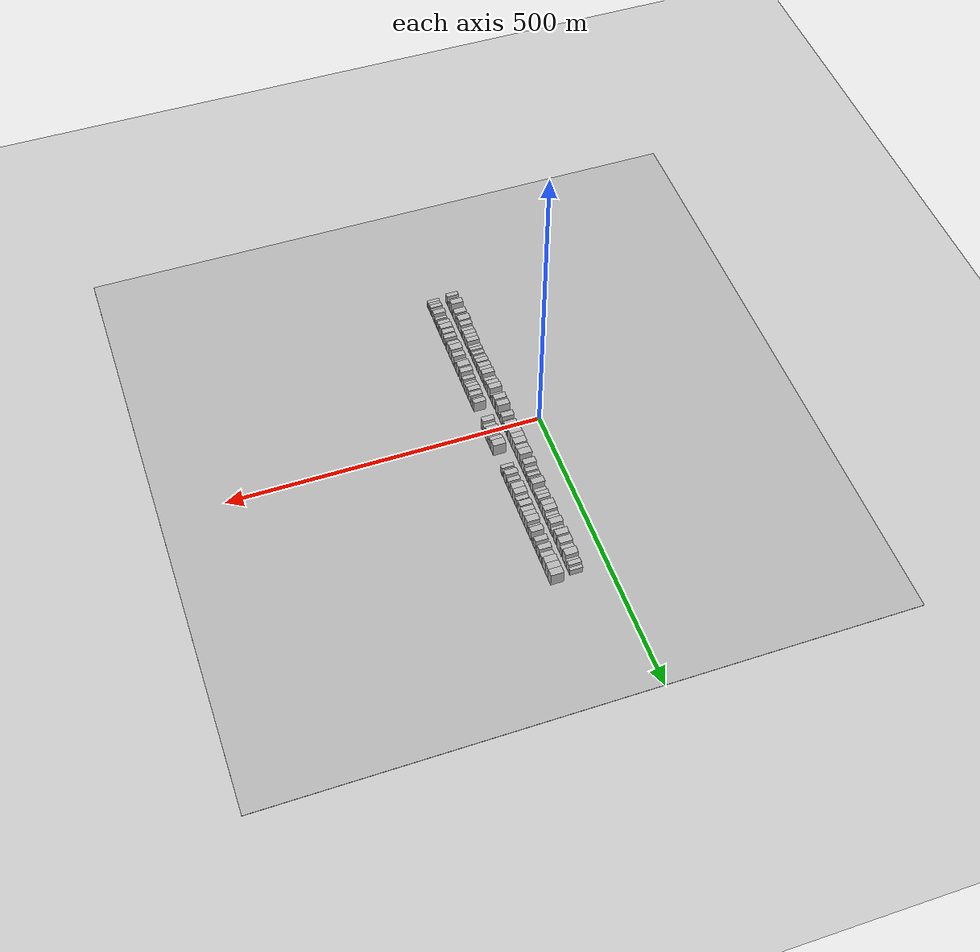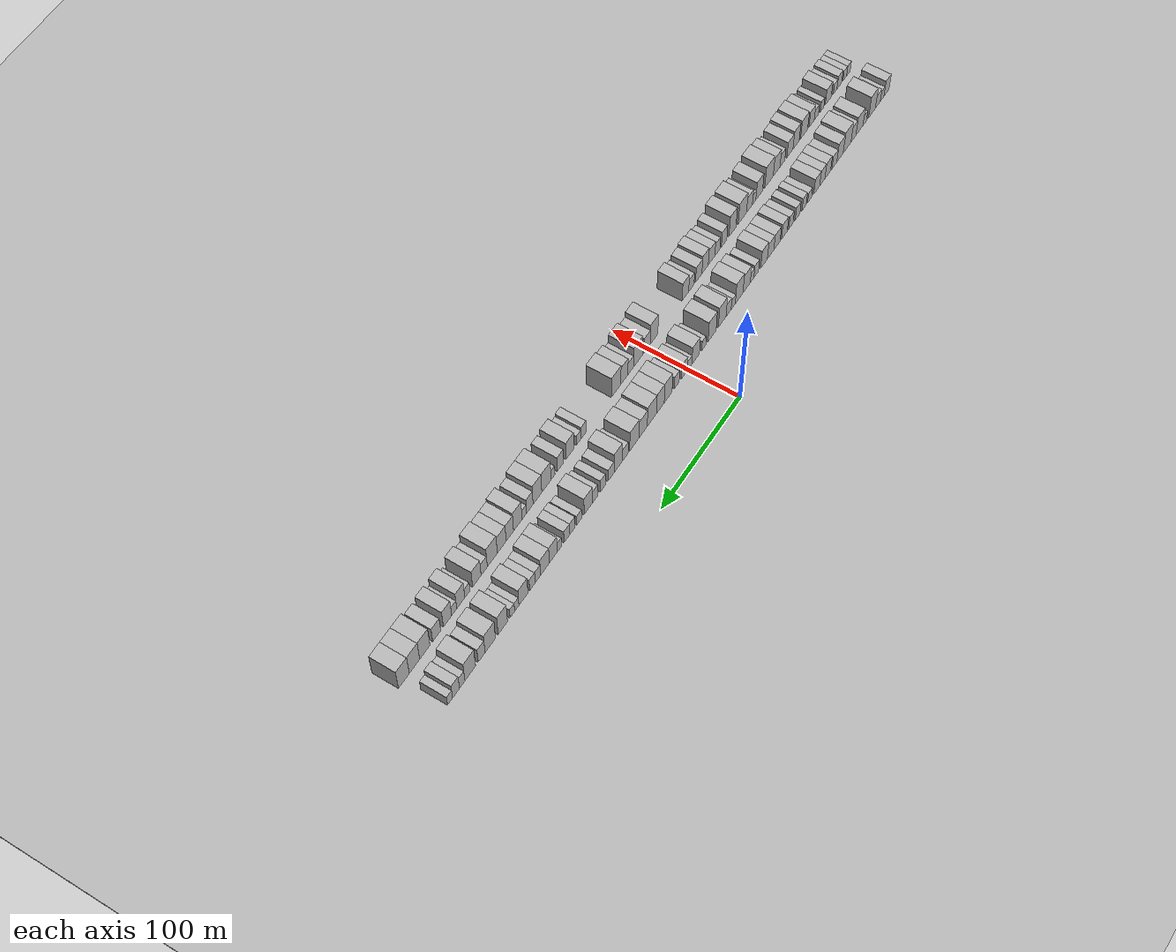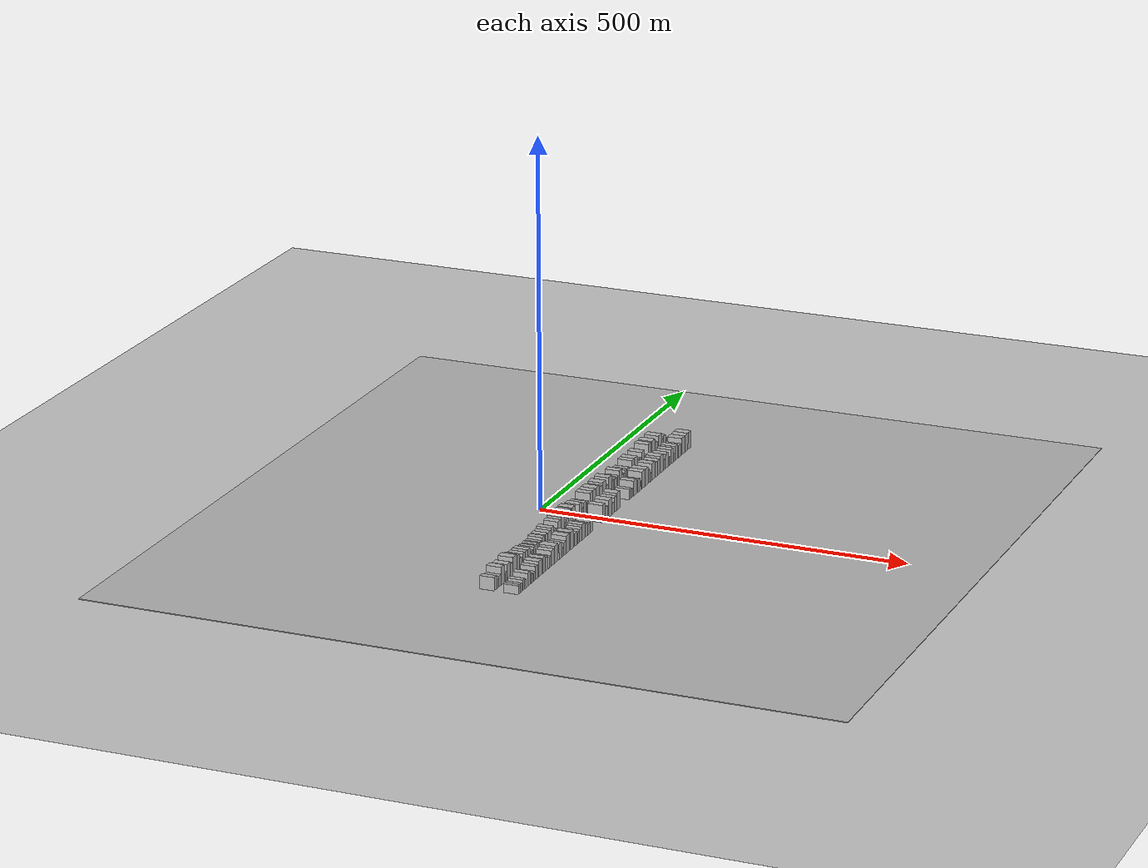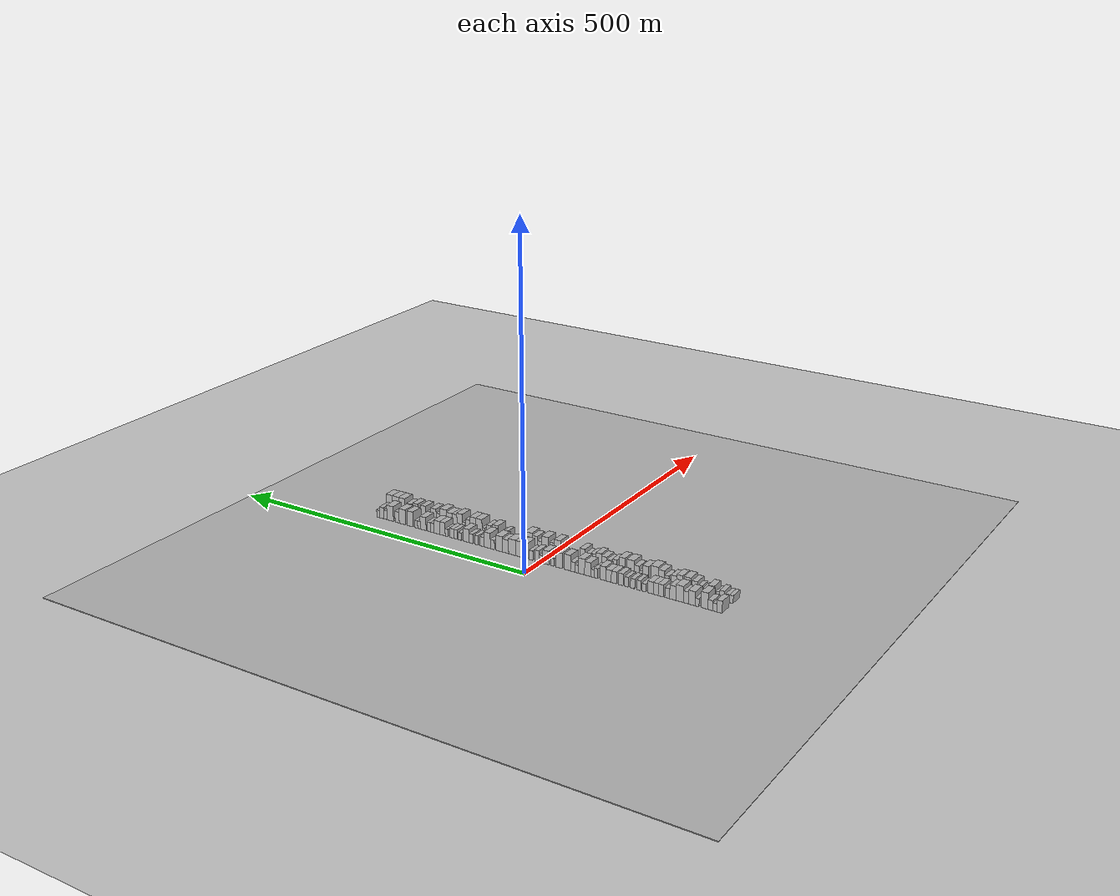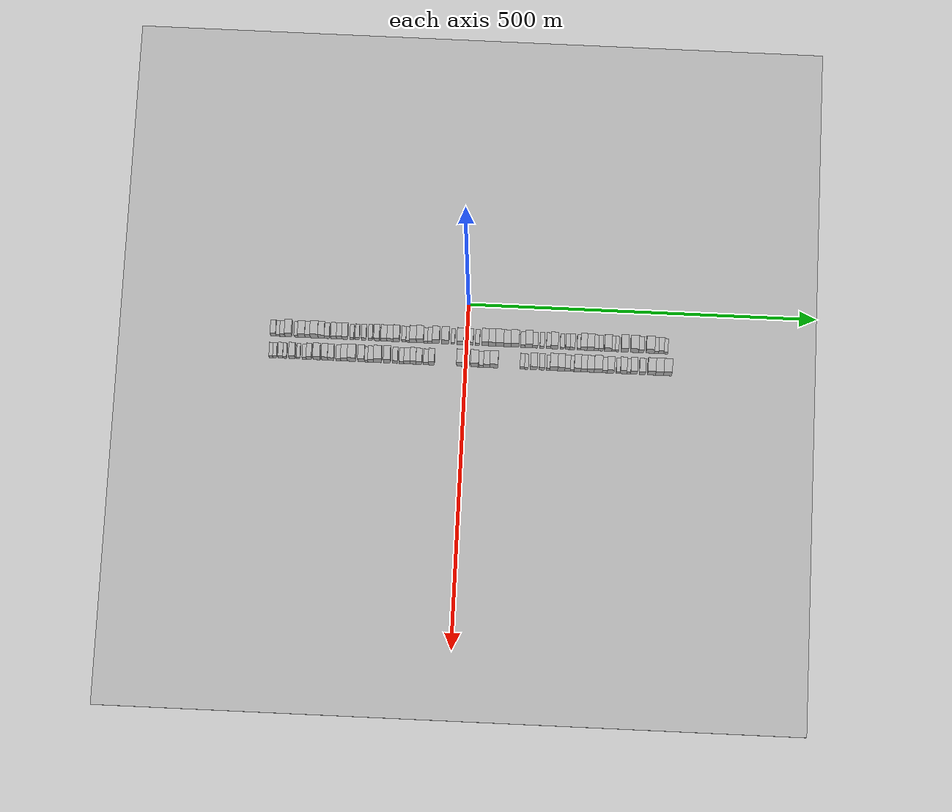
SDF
<?xml version="1.0" encoding="utf-8"?>

<sdf version="1.6">

   <world name="default">

      <gui fullscreen="0">

         <camera name="user_camera">

            <pose>-15 0 4.57585 0 0 0</pose>

            <view_controller>orbit</view_controller>

         </camera>

      </gui>

      <scene>

         <sky>

           <clouds>

             <speed>12</speed>

           </clouds>

         </sky>

         <ambient>0.4 0.4 0.4 1</ambient>

         <background>0.7 0.7 0.7 1</background>

         <shadows>1</shadows>

      </scene>

      <gravity>0 0 -9.8066</gravity>

      <magnetic_field>6e-06 2.3e-05 -4.2e-05</magnetic_field>

      <physics default="0" name="default_physics" type="ode">

         <ode>

            <solver>

               <type>quick</type>

               <iters>10</iters>

               <sor>1.0</sor>

               <use_dynamic_moi_rescaling>0</use_dynamic_moi_rescaling>

            </solver>

            <constraints>

               <cfm>0</cfm>

               <erp>0.2</erp>

               <contact_max_correcting_vel>100</contact_max_correcting_vel>

               <contact_surface_layer>0.001</contact_surface_layer>

            </constraints>

         </ode>

         <max_step_size>0.004</max_step_size>

         <real_time_factor>1</real_time_factor>

         <real_time_update_rate>250</real_time_update_rate>

      </physics>

      <light name="sun" type="directional">

         <cast_shadows>1</cast_shadows>

         <pose>0 0 10 0 0 0</pose>

         <diffuse>0.8 0.8 0.8 1</diffuse>

         <specular>0.2 0.2 0.2 1</specular>

         <attenuation>

            <range>1000</range>

            <constant>0.9</constant>

            <linear>0.01</linear>

            <quadratic>0.001</quadratic>

         </attenuation>

         <direction>-0.5 0.1 -0.9</direction>

      </light>

      <include>

         <name>ground_plane_1</name>

         <uri>model://HANNAS_ground_plane</uri>

         <pose>0 0 0  0 0 0</pose>

      </include>

      <include>

         <name>ground_plane_2</name>

         <uri>model://HANNAS_ground_plane</uri>

         <pose>100 0 0  0 0 0</pose>

      </include>

      <model name="building_1">

         <static>1</static>

         <pose frame="">50.0000 -278.0419 0 0.000000 0.000000 0.000000</pose>

         <link name="link">

            <pose frame="">0 0 9.00 0 0 0</pose>

            <collision name="collision">

               <geometry>

                  <box>

                     <size>20.0000 7.9161 18.0000</size>

                  </box>

               </geometry>

               <max_contacts>10</max_contacts>

               <surface>

                  <contact>

                     <ode/>

                  </contact>

                  <bounce/>

                  <friction>

                     <torsional>

                        <ode/>

                     </torsional>

                     <ode/>

                  </friction>

               </surface>

            </collision>

            <visual name="visual">

               <cast_shadows>0</cast_shadows>

               <geometry>

                  <box>

                     <size>20.0000 7.9161 18.0000</size>

                  </box>

               </geometry>

               <material>

                  <script>

                     <uri>model://HANNAS_wall/materials/scripts</uri>

                     <uri>model://HANNAS_wall/materials/textures</uri>

                     <name>vrc/HANNAS_wall</name>

                  </script>

               </material>

            </visual>

            <self_collide>0</self_collide>

            <enable_wind>0</enable_wind>

            <kinematic>0</kinematic>

         </link>

      </model>

      <model name="building_2">

         <static>1</static>

         <pose frame="">50.0000 -271.3548 0 0.000000 0.000000 0.000000</pose>

         <link name="link">

            <pose frame="">0 0 6.00 0 0 0</pose>

            <collision name="collision">

               <geometry>

                  <box>

                     <size>20.0000 5.4581 12.0000</size>

                  </box>

               </geometry>

               <max_contacts>10</max_contacts>

               <surface>

                  <contact>

                     <ode/>

                  </contact>

                  <bounce/>

                  <friction>

                     <torsional>

                        <ode/>

                     </torsional>

                     <ode/>

                  </friction>

               </surface>

            </collision>

            <visual name="visual">

               <cast_shadows>0</cast_shadows>

               <geometry>

                  <box>

                     <size>20.0000 5.4581 12.0000</size>

                  </box>

               </geometry>

               <material>

                  <script>

                     <uri>model://HANNAS_wall/materials/scripts</uri>

                     <uri>model://HANNAS_wall/materials/textures</uri>

                     <name>vrc/HANNAS_wall</name>

                  </script>

               </material>

            </visual>

            <self_collide>0</self_collide>

            <enable_wind>0</enable_wind>

            <kinematic>0</kinematic>

         </link>

      </model>

      <model name="building_3">

         <static>1</static>

         <pose frame="">50.0000 -264.9347 0 0.000000 0.000000 0.000000</pose>

         <link name="link">

            <pose frame="">0 0 7.50 0 0 0</pose>

            <collision name="collision">

               <geometry>

                  <box>

                     <size>20.0000 7.3822 15.0000</size>

                  </box>

               </geometry>

               <max_contacts>10</max_contacts>

               <surface>

                  <contact>

                     <ode/>

                  </contact>

                  <bounce/>

                  <friction>

                     <torsional>

                        <ode/>

                     </torsional>

                     <ode/>

                  </friction>

               </surface>

            </collision>

            <visual name="visual">

               <cast_shadows>0</cast_shadows>

               <geometry>

                  <box>

                     <size>20.0000 7.3822 15.0000</size>

                  </box>

               </geometry>

               <material>

                  <script>

                     <uri>model://HANNAS_wall/materials/scripts</uri>

                     <uri>model://HANNAS_wall/materials/textures</uri>

                     <name>vrc/HANNAS_wall</name>

                  </script>

               </material>

            </visual>

            <self_collide>0</self_collide>

            <enable_wind>0</enable_wind>

            <kinematic>0</kinematic>

         </link>

      </model>

      <model name="building_4">

         <static>1</static>

         <pose frame="">50.0000 -256.2046 0 0.000000 0.000000 0.000000</pose>

         <link name="link">

            <pose frame="">0 0 12.00 0 0 0</pose>

            <collision name="collision">

               <geometry>

                  <box>

                     <size>20.0000 10.0779 24.0000</size>

                  </box>

               </geometry>

               <max_contacts>10</max_contacts>

               <surface>

                  <contact>

                     <ode/>

                  </contact>

                  <bounce/>

                  <friction>

                     <torsional>

                        <ode/>

                     </torsional>

                     <ode/>

                  </friction>

               </surface>

            </collision>

            <visual name="visual">

               <cast_shadows>0</cast_shadows>

               <geometry>

                  <box>

                     <size>20.0000 10.0779 24.0000</size>

                  </box>

               </geometry>

               <material>

                  <script>

                     <uri>model://HANNAS_wall/materials/scripts</uri>

                     <uri>model://HANNAS_wall/materials/textures</uri>

                     <name>vrc/HANNAS_wall</name>

                  </script>

               </material>

            </visual>

            <self_collide>0</self_collide>

            <enable_wind>0</enable_wind>

            <kinematic>0</kinematic>

         </link>

      </model>

      <model name="building_5">

         <static>1</static>

         <pose frame="">50.0000 -245.4248 0 0.000000 0.000000 0.000000</pose>

         <link name="link">

            <pose frame="">0 0 6.00 0 0 0</pose>

            <collision name="collision">

               <geometry>

                  <box>

                     <size>20.0000 5.4817 12.0000</size>

                  </box>

               </geometry>

               <max_contacts>10</max_contacts>

               <surface>

                  <contact>

                     <ode/>

                  </contact>

                  <bounce/>

                  <friction>

                     <torsional>

                        <ode/>

                     </torsional>

                     <ode/>

                  </friction>

               </surface>

            </collision>

            <visual name="visual">

               <cast_shadows>0</cast_shadows>

               <geometry>

                  <box>

                     <size>20.0000 5.4817 12.0000</size>

                  </box>

               </geometry>

               <material>

                  <script>

                     <uri>model://HANNAS_wall/materials/scripts</uri>

                     <uri>model://HANNAS_wall/materials/textures</uri>

                     <name>vrc/HANNAS_wall</name>

                  </script>

               </material>

            </visual>

            <self_collide>0</self_collide>

            <enable_wind>0</enable_wind>

            <kinematic>0</kinematic>

         </link>

      </model>

      <model name="building_6">

         <static>1</static>

         <pose frame="">50.0000 -237.4997 0 0.000000 0.000000 0.000000</pose>

         <link name="link">

            <pose frame="">0 0 10.50 0 0 0</pose>

            <collision name="collision">

               <geometry>

                  <box>

                     <size>20.0000 10.3685 21.0000</size>

                  </box>

               </geometry>

               <max_contacts>10</max_contacts>

               <surface>

                  <contact>

                     <ode/>

                  </contact>

                  <bounce/>

                  <friction>

                     <torsional>

                        <ode/>

                     </torsional>

                     <ode/>

                  </friction>

               </surface>

            </collision>

            <visual name="visual">

               <cast_shadows>0</cast_shadows>

               <geometry>

                  <box>

                     <size>20.0000 10.3685 21.0000</size>

                  </box>

               </geometry>

               <material>

                  <script>

                     <uri>model://HANNAS_wall/materials/scripts</uri>

                     <uri>model://HANNAS_wall/materials/textures</uri>

                     <name>vrc/HANNAS_wall</name>

                  </script>

               </material>

            </visual>

            <self_collide>0</self_collide>

            <enable_wind>0</enable_wind>

            <kinematic>0</kinematic>

         </link>

      </model>

      <model name="building_7">

         <static>1</static>

         <pose frame="">50.0000 -228.6989 0 0.000000 0.000000 0.000000</pose>

         <link name="link">

            <pose frame="">0 0 9.00 0 0 0</pose>

            <collision name="collision">

               <geometry>

                  <box>

                     <size>20.0000 7.2332 18.0000</size>

                  </box>

               </geometry>

               <max_contacts>10</max_contacts>

               <surface>

                  <contact>

                     <ode/>

                  </contact>

                  <bounce/>

                  <friction>

                     <torsional>

                        <ode/>

                     </torsional>

                     <ode/>

                  </friction>

               </surface>

            </collision>

            <visual name="visual">

               <cast_shadows>0</cast_shadows>

               <geometry>

                  <box>

                     <size>20.0000 7.2332 18.0000</size>

                  </box>

               </geometry>

               <material>

                  <script>

                     <uri>model://HANNAS_wall/materials/scripts</uri>

                     <uri>model://HANNAS_wall/materials/textures</uri>

                     <name>vrc/HANNAS_wall</name>

                  </script>

               </material>

            </visual>

            <self_collide>0</self_collide>

            <enable_wind>0</enable_wind>

            <kinematic>0</kinematic>

         </link>

      </model>

      <model name="building_8">

         <static>1</static>

         <pose frame="">50.0000 -219.3549 0 0.000000 0.000000 0.000000</pose>

         <link name="link">

            <pose frame="">0 0 12.00 0 0 0</pose>

            <collision name="collision">

               <geometry>

                  <box>

                     <size>20.0000 11.4548 24.0000</size>

                  </box>

               </geometry>

               <max_contacts>10</max_contacts>

               <surface>

                  <contact>

                     <ode/>

                  </contact>

                  <bounce/>

                  <friction>

                     <torsional>

                        <ode/>

                     </torsional>

                     <ode/>

                  </friction>

               </surface>

            </collision>

            <visual name="visual">

               <cast_shadows>0</cast_shadows>

               <geometry>

                  <box>

                     <size>20.0000 11.4548 24.0000</size>

                  </box>

               </geometry>

               <material>

                  <script>

                     <uri>model://HANNAS_wall/materials/scripts</uri>

                     <uri>model://HANNAS_wall/materials/textures</uri>

                     <name>vrc/HANNAS_wall</name>

                  </script>

               </material>

            </visual>

            <self_collide>0</self_collide>

            <enable_wind>0</enable_wind>

            <kinematic>0</kinematic>

         </link>

      </model>

      <model name="building_9">

         <static>1</static>

         <pose frame="">50.0000 -209.0306 0 0.000000 0.000000 0.000000</pose>

         <link name="link">

            <pose frame="">0 0 10.50 0 0 0</pose>

            <collision name="collision">

               <geometry>

                  <box>

                     <size>20.0000 9.1938 21.0000</size>

                  </box>

               </geometry>

               <max_contacts>10</max_contacts>

               <surface>

                  <contact>

                     <ode/>

                  </contact>

                  <bounce/>

                  <friction>

                     <torsional>

                        <ode/>

                     </torsional>

                     <ode/>

                  </friction>

               </surface>

            </collision>

            <visual name="visual">

               <cast_shadows>0</cast_shadows>

               <geometry>

                  <box>

                     <size>20.0000 9.1938 21.0000</size>

                  </box>

               </geometry>

               <material>

                  <script>

                     <uri>model://HANNAS_wall/materials/scripts</uri>

                     <uri>model://HANNAS_wall/materials/textures</uri>

                     <name>vrc/HANNAS_wall</name>

                  </script>

               </material>

            </visual>

            <self_collide>0</self_collide>

            <enable_wind>0</enable_wind>

            <kinematic>0</kinematic>

         </link>

      </model>

      <model name="building_10">

         <static>1</static>

         <pose frame="">50.0000 -200.8286 0 0.000000 0.000000 0.000000</pose>

         <link name="link">

            <pose frame="">0 0 7.50 0 0 0</pose>

            <collision name="collision">

               <geometry>

                  <box>

                     <size>20.0000 7.2102 15.0000</size>

                  </box>

               </geometry>

               <max_contacts>10</max_contacts>

               <surface>

                  <contact>

                     <ode/>

                  </contact>

                  <bounce/>

                  <friction>

                     <torsional>

                        <ode/>

                     </torsional>

                     <ode/>

                  </friction>

               </surface>

            </collision>

            <visual name="visual">

               <cast_shadows>0</cast_shadows>

               <geometry>

                  <box>

                     <size>20.0000 7.2102 15.0000</size>

                  </box>

               </geometry>

               <material>

                  <script>

                     <uri>model://HANNAS_wall/materials/scripts</uri>

                     <uri>model://HANNAS_wall/materials/textures</uri>

                     <name>vrc/HANNAS_wall</name>

                  </script>

               </material>

            </visual>

            <self_collide>0</self_collide>

            <enable_wind>0</enable_wind>

            <kinematic>0</kinematic>

         </link>

      </model>

      <model name="building_11">

         <static>1</static>

         <pose frame="">50.0000 -191.1680 0 0.000000 0.000000 0.000000</pose>

         <link name="link">

            <pose frame="">0 0 9.00 0 0 0</pose>

            <collision name="collision">

               <geometry>

                  <box>

                     <size>20.0000 8.1109 18.0000</size>

                  </box>

               </geometry>

               <max_contacts>10</max_contacts>

               <surface>

                  <contact>

                     <ode/>

                  </contact>

                  <bounce/>

                  <friction>

                     <torsional>

                        <ode/>

                     </torsional>

                     <ode/>

                  </friction>

               </surface>

            </collision>

            <visual name="visual">

               <cast_shadows>0</cast_shadows>

               <geometry>

                  <box>

                     <size>20.0000 8.1109 18.0000</size>

                  </box>

               </geometry>

               <material>

                  <script>

                     <uri>model://HANNAS_wall/materials/scripts</uri>

                     <uri>model://HANNAS_wall/materials/textures</uri>

                     <name>vrc/HANNAS_wall</name>

                  </script>

               </material>

            </visual>

            <self_collide>0</self_collide>

            <enable_wind>0</enable_wind>

            <kinematic>0</kinematic>

         </link>

      </model>

      <model name="building_12">

         <static>1</static>

         <pose frame="">50.0000 -183.3251 0 0.000000 0.000000 0.000000</pose>

         <link name="link">

            <pose frame="">0 0 9.00 0 0 0</pose>

            <collision name="collision">

               <geometry>

                  <box>

                     <size>20.0000 7.5751 18.0000</size>

                  </box>

               </geometry>

               <max_contacts>10</max_contacts>

               <surface>

                  <contact>

                     <ode/>

                  </contact>

                  <bounce/>

                  <friction>

                     <torsional>

                        <ode/>

                     </torsional>

                     <ode/>

                  </friction>

               </surface>

            </collision>

            <visual name="visual">

               <cast_shadows>0</cast_shadows>

               <geometry>

                  <box>

                     <size>20.0000 7.5751 18.0000</size>

                  </box>

               </geometry>

               <material>

                  <script>

                     <uri>model://HANNAS_wall/materials/scripts</uri>

                     <uri>model://HANNAS_wall/materials/textures</uri>

                     <name>vrc/HANNAS_wall</name>

                  </script>

               </material>

            </visual>

            <self_collide>0</self_collide>

            <enable_wind>0</enable_wind>

            <kinematic>0</kinematic>

         </link>

      </model>

      <model name="building_13">

         <static>1</static>

         <pose frame="">50.0000 -175.3021 0 0.000000 0.000000 0.000000</pose>

         <link name="link">

            <pose frame="">0 0 9.00 0 0 0</pose>

            <collision name="collision">

               <geometry>

                  <box>

                     <size>20.0000 8.4709 18.0000</size>

                  </box>

               </geometry>

               <max_contacts>10</max_contacts>

               <surface>

                  <contact>

                     <ode/>

                  </contact>

                  <bounce/>

                  <friction>

                     <torsional>

                        <ode/>

                     </torsional>

                     <ode/>

                  </friction>

               </surface>

            </collision>

            <visual name="visual">

               <cast_shadows>0</cast_shadows>

               <geometry>

                  <box>

                     <size>20.0000 8.4709 18.0000</size>

                  </box>

               </geometry>

               <material>

                  <script>

                     <uri>model://HANNAS_wall/materials/scripts</uri>

                     <uri>model://HANNAS_wall/materials/textures</uri>

                     <name>vrc/HANNAS_wall</name>

                  </script>

               </material>

            </visual>

            <self_collide>0</self_collide>

            <enable_wind>0</enable_wind>

            <kinematic>0</kinematic>

         </link>

      </model>

      <model name="building_14">

         <static>1</static>

         <pose frame="">50.0000 -165.2082 0 0.000000 0.000000 0.000000</pose>

         <link name="link">

            <pose frame="">0 0 6.00 0 0 0</pose>

            <collision name="collision">

               <geometry>

                  <box>

                     <size>20.0000 5.7168 12.0000</size>

                  </box>

               </geometry>

               <max_contacts>10</max_contacts>

               <surface>

                  <contact>

                     <ode/>

                  </contact>

                  <bounce/>

                  <friction>

                     <torsional>

                        <ode/>

                     </torsional>

                     <ode/>

                  </friction>

               </surface>

            </collision>

            <visual name="visual">

               <cast_shadows>0</cast_shadows>

               <geometry>

                  <box>

                     <size>20.0000 5.7168 12.0000</size>

                  </box>

               </geometry>

               <material>

                  <script>

                     <uri>model://HANNAS_wall/materials/scripts</uri>

                     <uri>model://HANNAS_wall/materials/textures</uri>

                     <name>vrc/HANNAS_wall</name>

                  </script>

               </material>

            </visual>

            <self_collide>0</self_collide>

            <enable_wind>0</enable_wind>

            <kinematic>0</kinematic>

         </link>

      </model>

      <model name="building_15">

         <static>1</static>

         <pose frame="">50.0000 -157.3259 0 0.000000 0.000000 0.000000</pose>

         <link name="link">

            <pose frame="">0 0 7.50 0 0 0</pose>

            <collision name="collision">

               <geometry>

                  <box>

                     <size>20.0000 6.0478 15.0000</size>

                  </box>

               </geometry>

               <max_contacts>10</max_contacts>

               <surface>

                  <contact>

                     <ode/>

                  </contact>

                  <bounce/>

                  <friction>

                     <torsional>

                        <ode/>

                     </torsional>

                     <ode/>

                  </friction>

               </surface>

            </collision>

            <visual name="visual">

               <cast_shadows>0</cast_shadows>

               <geometry>

                  <box>

                     <size>20.0000 6.0478 15.0000</size>

                  </box>

               </geometry>

               <material>

                  <script>

                     <uri>model://HANNAS_wall/materials/scripts</uri>

                     <uri>model://HANNAS_wall/materials/textures</uri>

                     <name>vrc/HANNAS_wall</name>

                  </script>

               </material>

            </visual>

            <self_collide>0</self_collide>

            <enable_wind>0</enable_wind>

            <kinematic>0</kinematic>

         </link>

      </model>

      <model name="building_16">

         <static>1</static>

         <pose frame="">50.0000 -148.0049 0 0.000000 0.000000 0.000000</pose>

         <link name="link">

            <pose frame="">0 0 7.50 0 0 0</pose>

            <collision name="collision">

               <geometry>

                  <box>

                     <size>20.0000 6.5941 15.0000</size>

                  </box>

               </geometry>

               <max_contacts>10</max_contacts>

               <surface>

                  <contact>

                     <ode/>

                  </contact>

                  <bounce/>

                  <friction>

                     <torsional>

                        <ode/>

                     </torsional>

                     <ode/>

                  </friction>

               </surface>

            </collision>

            <visual name="visual">

               <cast_shadows>0</cast_shadows>

               <geometry>

                  <box>

                     <size>20.0000 6.5941 15.0000</size>

                  </box>

               </geometry>

               <material>

                  <script>

                     <uri>model://HANNAS_wall/materials/scripts</uri>

                     <uri>model://HANNAS_wall/materials/textures</uri>

                     <name>vrc/HANNAS_wall</name>

                  </script>

               </material>

            </visual>

            <self_collide>0</self_collide>

            <enable_wind>0</enable_wind>

            <kinematic>0</kinematic>

         </link>

      </model>

      <model name="building_17">

         <static>1</static>

         <pose frame="">50.0000 -138.6632 0 0.000000 0.000000 0.000000</pose>

         <link name="link">

            <pose frame="">0 0 7.50 0 0 0</pose>

            <collision name="collision">

               <geometry>

                  <box>

                     <size>20.0000 6.0894 15.0000</size>

                  </box>

               </geometry>

               <max_contacts>10</max_contacts>

               <surface>

                  <contact>

                     <ode/>

                  </contact>

                  <bounce/>

                  <friction>

                     <torsional>

                        <ode/>

                     </torsional>

                     <ode/>

                  </friction>

               </surface>

            </collision>

            <visual name="visual">

               <cast_shadows>0</cast_shadows>

               <geometry>

                  <box>

                     <size>20.0000 6.0894 15.0000</size>

                  </box>

               </geometry>

               <material>

                  <script>

                     <uri>model://HANNAS_wall/materials/scripts</uri>

                     <uri>model://HANNAS_wall/materials/textures</uri>

                     <name>vrc/HANNAS_wall</name>

                  </script>

               </material>

            </visual>

            <self_collide>0</self_collide>

            <enable_wind>0</enable_wind>

            <kinematic>0</kinematic>

         </link>

      </model>

      <model name="building_18">

         <static>1</static>

         <pose frame="">50.0000 -129.5498 0 0.000000 0.000000 0.000000</pose>

         <link name="link">

            <pose frame="">0 0 9.00 0 0 0</pose>

            <collision name="collision">

               <geometry>

                  <box>

                     <size>20.0000 8.1373 18.0000</size>

                  </box>

               </geometry>

               <max_contacts>10</max_contacts>

               <surface>

                  <contact>

                     <ode/>

                  </contact>

                  <bounce/>

                  <friction>

                     <torsional>

                        <ode/>

                     </torsional>

                     <ode/>

                  </friction>

               </surface>

            </collision>

            <visual name="visual">

               <cast_shadows>0</cast_shadows>

               <geometry>

                  <box>

                     <size>20.0000 8.1373 18.0000</size>

                  </box>

               </geometry>

               <material>

                  <script>

                     <uri>model://HANNAS_wall/materials/scripts</uri>

                     <uri>model://HANNAS_wall/materials/textures</uri>

                     <name>vrc/HANNAS_wall</name>

                  </script>

               </material>

            </visual>

            <self_collide>0</self_collide>

            <enable_wind>0</enable_wind>

            <kinematic>0</kinematic>

         </link>

      </model>

      <model name="building_19">

         <static>1</static>

         <pose frame="">50.0000 -119.1275 0 0.000000 0.000000 0.000000</pose>

         <link name="link">

            <pose frame="">0 0 9.00 0 0 0</pose>

            <collision name="collision">

               <geometry>

                  <box>

                     <size>20.0000 8.7075 18.0000</size>

                  </box>

               </geometry>

               <max_contacts>10</max_contacts>

               <surface>

                  <contact>

                     <ode/>

                  </contact>

                  <bounce/>

                  <friction>

                     <torsional>

                        <ode/>

                     </torsional>

                     <ode/>

                  </friction>

               </surface>

            </collision>

            <visual name="visual">

               <cast_shadows>0</cast_shadows>

               <geometry>

                  <box>

                     <size>20.0000 8.7075 18.0000</size>

                  </box>

               </geometry>

               <material>

                  <script>

                     <uri>model://HANNAS_wall/materials/scripts</uri>

                     <uri>model://HANNAS_wall/materials/textures</uri>

                     <name>vrc/HANNAS_wall</name>

                  </script>

               </material>

            </visual>

            <self_collide>0</self_collide>

            <enable_wind>0</enable_wind>

            <kinematic>0</kinematic>

         </link>

      </model>

      <model name="building_20">

         <static>1</static>

         <pose frame="">50.0000 -110.3166 0 0.000000 0.000000 0.000000</pose>

         <link name="link">

            <pose frame="">0 0 9.00 0 0 0</pose>

            <collision name="collision">

               <geometry>

                  <box>

                     <size>20.0000 8.9142 18.0000</size>

                  </box>

               </geometry>

               <max_contacts>10</max_contacts>

               <surface>

                  <contact>

                     <ode/>

                  </contact>

                  <bounce/>

                  <friction>

                     <torsional>

                        <ode/>

                     </torsional>

                     <ode/>

                  </friction>

               </surface>

            </collision>

            <visual name="visual">

               <cast_shadows>0</cast_shadows>

               <geometry>

                  <box>

                     <size>20.0000 8.9142 18.0000</size>

                  </box>

               </geometry>

               <material>

                  <script>

                     <uri>model://HANNAS_wall/materials/scripts</uri>

                     <uri>model://HANNAS_wall/materials/textures</uri>

                     <name>vrc/HANNAS_wall</name>

                  </script>

               </material>

            </visual>

            <self_collide>0</self_collide>

            <enable_wind>0</enable_wind>

            <kinematic>0</kinematic>

         </link>

      </model>

      <model name="building_21">

         <static>1</static>

         <pose frame="">50.0000 -101.2761 0 0.000000 0.000000 0.000000</pose>

         <link name="link">

            <pose frame="">0 0 10.50 0 0 0</pose>

            <collision name="collision">

               <geometry>

                  <box>

                     <size>20.0000 9.1668 21.0000</size>

                  </box>

               </geometry>

               <max_contacts>10</max_contacts>

               <surface>

                  <contact>

                     <ode/>

                  </contact>

                  <bounce/>

                  <friction>

                     <torsional>

                        <ode/>

                     </torsional>

                     <ode/>

                  </friction>

               </surface>

            </collision>

            <visual name="visual">

               <cast_shadows>0</cast_shadows>

               <geometry>

                  <box>

                     <size>20.0000 9.1668 21.0000</size>

                  </box>

               </geometry>

               <material>

                  <script>

                     <uri>model://HANNAS_wall/materials/scripts</uri>

                     <uri>model://HANNAS_wall/materials/textures</uri>

                     <name>vrc/HANNAS_wall</name>

                  </script>

               </material>

            </visual>

            <self_collide>0</self_collide>

            <enable_wind>0</enable_wind>

            <kinematic>0</kinematic>

         </link>

      </model>

      <model name="building_22">

         <static>1</static>

         <pose frame="">50.0000 -90.5518 0 0.000000 0.000000 0.000000</pose>

         <link name="link">

            <pose frame="">0 0 7.50 0 0 0</pose>

            <collision name="collision">

               <geometry>

                  <box>

                     <size>20.0000 6.2818 15.0000</size>

                  </box>

               </geometry>

               <max_contacts>10</max_contacts>

               <surface>

                  <contact>

                     <ode/>

                  </contact>

                  <bounce/>

                  <friction>

                     <torsional>

                        <ode/>

                     </torsional>

                     <ode/>

                  </friction>

               </surface>

            </collision>

            <visual name="visual">

               <cast_shadows>0</cast_shadows>

               <geometry>

                  <box>

                     <size>20.0000 6.2818 15.0000</size>

                  </box>

               </geometry>

               <material>

                  <script>

                     <uri>model://HANNAS_wall/materials/scripts</uri>

                     <uri>model://HANNAS_wall/materials/textures</uri>

                     <name>vrc/HANNAS_wall</name>

                  </script>

               </material>

            </visual>

            <self_collide>0</self_collide>

            <enable_wind>0</enable_wind>

            <kinematic>0</kinematic>

         </link>

      </model>

      <model name="building_23">

         <static>1</static>

         <pose frame="">50.0000 -84.8986 0 0.000000 0.000000 0.000000</pose>

         <link name="link">

            <pose frame="">0 0 6.00 0 0 0</pose>

            <collision name="collision">

               <geometry>

                  <box>

                     <size>20.0000 5.0246 12.0000</size>

                  </box>

               </geometry>

               <max_contacts>10</max_contacts>

               <surface>

                  <contact>

                     <ode/>

                  </contact>

                  <bounce/>

                  <friction>

                     <torsional>

                        <ode/>

                     </torsional>

                     <ode/>

                  </friction>

               </surface>

            </collision>

            <visual name="visual">

               <cast_shadows>0</cast_shadows>

               <geometry>

                  <box>

                     <size>20.0000 5.0246 12.0000</size>

                  </box>

               </geometry>

               <material>

                  <script>

                     <uri>model://HANNAS_wall/materials/scripts</uri>

                     <uri>model://HANNAS_wall/materials/textures</uri>

                     <name>vrc/HANNAS_wall</name>

                  </script>

               </material>

            </visual>

            <self_collide>0</self_collide>

            <enable_wind>0</enable_wind>

            <kinematic>0</kinematic>

         </link>

      </model>

      <model name="building_24">

         <static>1</static>

         <pose frame="">50.0000 -77.4337 0 0.000000 0.000000 0.000000</pose>

         <link name="link">

            <pose frame="">0 0 10.50 0 0 0</pose>

            <collision name="collision">

               <geometry>

                  <box>

                     <size>20.0000 9.9053 21.0000</size>

                  </box>

               </geometry>

               <max_contacts>10</max_contacts>

               <surface>

                  <contact>

                     <ode/>

                  </contact>

                  <bounce/>

                  <friction>

                     <torsional>

                        <ode/>

                     </torsional>

                     <ode/>

                  </friction>

               </surface>

            </collision>

            <visual name="visual">

               <cast_shadows>0</cast_shadows>

               <geometry>

                  <box>

                     <size>20.0000 9.9053 21.0000</size>

                  </box>

               </geometry>

               <material>

                  <script>

                     <uri>model://HANNAS_wall/materials/scripts</uri>

                     <uri>model://HANNAS_wall/materials/textures</uri>

                     <name>vrc/HANNAS_wall</name>

                  </script>

               </material>

            </visual>

            <self_collide>0</self_collide>

            <enable_wind>0</enable_wind>

            <kinematic>0</kinematic>

         </link>

      </model>

      <model name="building_25">

         <static>1</static>

         <pose frame="">50.0000 -67.3081 0 0.000000 0.000000 0.000000</pose>

         <link name="link">

            <pose frame="">0 0 12.00 0 0 0</pose>

            <collision name="collision">

               <geometry>

                  <box>

                     <size>20.0000 10.3458 24.0000</size>

                  </box>

               </geometry>

               <max_contacts>10</max_contacts>

               <surface>

                  <contact>

                     <ode/>

                  </contact>

                  <bounce/>

                  <friction>

                     <torsional>

                        <ode/>

                     </torsional>

                     <ode/>

                  </friction>

               </surface>

            </collision>

            <visual name="visual">

               <cast_shadows>0</cast_shadows>

               <geometry>

                  <box>

                     <size>20.0000 10.3458 24.0000</size>

                  </box>

               </geometry>

               <material>

                  <script>

                     <uri>model://HANNAS_wall/materials/scripts</uri>

                     <uri>model://HANNAS_wall/materials/textures</uri>

                     <name>vrc/HANNAS_wall</name>

                  </script>

               </material>

            </visual>

            <self_collide>0</self_collide>

            <enable_wind>0</enable_wind>

            <kinematic>0</kinematic>

         </link>

      </model>

      <model name="building_26">

         <static>1</static>

         <pose frame="">50.0000 -59.3123 0 0.000000 0.000000 0.000000</pose>

         <link name="link">

            <pose frame="">0 0 6.00 0 0 0</pose>

            <collision name="collision">

               <geometry>

                  <box>

                     <size>20.0000 5.6458 12.0000</size>

                  </box>

               </geometry>

               <max_contacts>10</max_contacts>

               <surface>

                  <contact>

                     <ode/>

                  </contact>

                  <bounce/>

                  <friction>

                     <torsional>

                        <ode/>

                     </torsional>

                     <ode/>

                  </friction>

               </surface>

            </collision>

            <visual name="visual">

               <cast_shadows>0</cast_shadows>

               <geometry>

                  <box>

                     <size>20.0000 5.6458 12.0000</size>

                  </box>

               </geometry>

               <material>

                  <script>

                     <uri>model://HANNAS_wall/materials/scripts</uri>

                     <uri>model://HANNAS_wall/materials/textures</uri>

                     <name>vrc/HANNAS_wall</name>

                  </script>

               </material>

            </visual>

            <self_collide>0</self_collide>

            <enable_wind>0</enable_wind>

            <kinematic>0</kinematic>

         </link>

      </model>

      <model name="building_27">

         <static>1</static>

         <pose frame="">50.0000 -53.0822 0 0.000000 0.000000 0.000000</pose>

         <link name="link">

            <pose frame="">0 0 7.50 0 0 0</pose>

            <collision name="collision">

               <geometry>

                  <box>

                     <size>20.0000 6.8145 15.0000</size>

                  </box>

               </geometry>

               <max_contacts>10</max_contacts>

               <surface>

                  <contact>

                     <ode/>

                  </contact>

                  <bounce/>

                  <friction>

                     <torsional>

                        <ode/>

                     </torsional>

                     <ode/>

                  </friction>

               </surface>

            </collision>

            <visual name="visual">

               <cast_shadows>0</cast_shadows>

               <geometry>

                  <box>

                     <size>20.0000 6.8145 15.0000</size>

                  </box>

               </geometry>

               <material>

                  <script>

                     <uri>model://HANNAS_wall/materials/scripts</uri>

                     <uri>model://HANNAS_wall/materials/textures</uri>

                     <name>vrc/HANNAS_wall</name>

                  </script>

               </material>

            </visual>

            <self_collide>0</self_collide>

            <enable_wind>0</enable_wind>

            <kinematic>0</kinematic>

         </link>

      </model>

      <model name="building_28">

         <static>1</static>

         <pose frame="">50.0000 -44.5642 0 0.000000 0.000000 0.000000</pose>

         <link name="link">

            <pose frame="">0 0 12.00 0 0 0</pose>

            <collision name="collision">

               <geometry>

                  <box>

                     <size>20.0000 10.2215 24.0000</size>

                  </box>

               </geometry>

               <max_contacts>10</max_contacts>

               <surface>

                  <contact>

                     <ode/>

                  </contact>

                  <bounce/>

                  <friction>

                     <torsional>

                        <ode/>

                     </torsional>

                     <ode/>

                  </friction>

               </surface>

            </collision>

            <visual name="visual">

               <cast_shadows>0</cast_shadows>

               <geometry>

                  <box>

                     <size>20.0000 10.2215 24.0000</size>

                  </box>

               </geometry>

               <material>

                  <script>

                     <uri>model://HANNAS_wall/materials/scripts</uri>

                     <uri>model://HANNAS_wall/materials/textures</uri>

                     <name>vrc/HANNAS_wall</name>

                  </script>

               </material>

            </visual>

            <self_collide>0</self_collide>

            <enable_wind>0</enable_wind>

            <kinematic>0</kinematic>

         </link>

      </model>

      <model name="building_29">

         <static>1</static>

         <pose frame="">50.0000 -31.1216 0 0.000000 0.000000 0.000000</pose>

         <link name="link">

            <pose frame="">0 0 12.00 0 0 0</pose>

            <collision name="collision">

               <geometry>

                  <box>

                     <size>20.0000 10.6637 24.0000</size>

                  </box>

               </geometry>

               <max_contacts>10</max_contacts>

               <surface>

                  <contact>

                     <ode/>

                  </contact>

                  <bounce/>

                  <friction>

                     <torsional>

                        <ode/>

                     </torsional>

                     <ode/>

                  </friction>

               </surface>

            </collision>

            <visual name="visual">

               <cast_shadows>0</cast_shadows>

               <geometry>

                  <box>

                     <size>20.0000 10.6637 24.0000</size>

                  </box>

               </geometry>

               <material>

                  <script>

                     <uri>model://HANNAS_wall/materials/scripts</uri>

                     <uri>model://HANNAS_wall/materials/textures</uri>

                     <name>vrc/HANNAS_wall</name>

                  </script>

               </material>

            </visual>

            <self_collide>0</self_collide>

            <enable_wind>0</enable_wind>

            <kinematic>0</kinematic>

         </link>

      </model>

      <model name="building_30">

         <static>1</static>

         <pose frame="">50.0000 -20.1444 0 0.000000 0.000000 0.000000</pose>

         <link name="link">

            <pose frame="">0 0 6.00 0 0 0</pose>

            <collision name="collision">

               <geometry>

                  <box>

                     <size>20.0000 5.2907 12.0000</size>

                  </box>

               </geometry>

               <max_contacts>10</max_contacts>

               <surface>

                  <contact>

                     <ode/>

                  </contact>

                  <bounce/>

                  <friction>

                     <torsional>

                        <ode/>

                     </torsional>

                     <ode/>

                  </friction>

               </surface>

            </collision>

            <visual name="visual">

               <cast_shadows>0</cast_shadows>

               <geometry>

                  <box>

                     <size>20.0000 5.2907 12.0000</size>

                  </box>

               </geometry>

               <material>

                  <script>

                     <uri>model://HANNAS_wall/materials/scripts</uri>

                     <uri>model://HANNAS_wall/materials/textures</uri>

                     <name>vrc/HANNAS_wall</name>

                  </script>

               </material>

            </visual>

            <self_collide>0</self_collide>

            <enable_wind>0</enable_wind>

            <kinematic>0</kinematic>

         </link>

      </model>

      <model name="building_31">

         <static>1</static>

         <pose frame="">50.0000 -9.5176 0 0.000000 0.000000 0.000000</pose>

         <link name="link">

            <pose frame="">0 0 10.50 0 0 0</pose>

            <collision name="collision">

               <geometry>

                  <box>

                     <size>20.0000 9.9630 21.0000</size>

                  </box>

               </geometry>

               <max_contacts>10</max_contacts>

               <surface>

                  <contact>

                     <ode/>

                  </contact>

                  <bounce/>

                  <friction>

                     <torsional>

                        <ode/>

                     </torsional>

                     <ode/>

                  </friction>

               </surface>

            </collision>

            <visual name="visual">

               <cast_shadows>0</cast_shadows>

               <geometry>

                  <box>

                     <size>20.0000 9.9630 21.0000</size>

                  </box>

               </geometry>

               <material>

                  <script>

                     <uri>model://HANNAS_wall/materials/scripts</uri>

                     <uri>model://HANNAS_wall/materials/textures</uri>

                     <name>vrc/HANNAS_wall</name>

                  </script>

               </material>

            </visual>

            <self_collide>0</self_collide>

            <enable_wind>0</enable_wind>

            <kinematic>0</kinematic>

         </link>

      </model>

      <model name="building_32">

         <static>1</static>

         <pose frame="">50.0000 -1.6180 0 0.000000 0.000000 0.000000</pose>

         <link name="link">

            <pose frame="">0 0 6.00 0 0 0</pose>

            <collision name="collision">

               <geometry>

                  <box>

                     <size>20.0000 5.8362 12.0000</size>

                  </box>

               </geometry>

               <max_contacts>10</max_contacts>

               <surface>

                  <contact>

                     <ode/>

                  </contact>

                  <bounce/>

                  <friction>

                     <torsional>

                        <ode/>

                     </torsional>

                     <ode/>

                  </friction>

               </surface>

            </collision>

            <visual name="visual">

               <cast_shadows>0</cast_shadows>

               <geometry>

                  <box>

                     <size>20.0000 5.8362 12.0000</size>

                  </box>

               </geometry>

               <material>

                  <script>

                     <uri>model://HANNAS_wall/materials/scripts</uri>

                     <uri>model://HANNAS_wall/materials/textures</uri>

                     <name>vrc/HANNAS_wall</name>

                  </script>

               </material>

            </visual>

            <self_collide>0</self_collide>

            <enable_wind>0</enable_wind>

            <kinematic>0</kinematic>

         </link>

      </model>

      <model name="building_33">

         <static>1</static>

         <pose frame="">50.0000 5.1053 0 0.000000 0.000000 0.000000</pose>

         <link name="link">

            <pose frame="">0 0 9.00 0 0 0</pose>

            <collision name="collision">

               <geometry>

                  <box>

                     <size>20.0000 7.6104 18.0000</size>

                  </box>

               </geometry>

               <max_contacts>10</max_contacts>

               <surface>

                  <contact>

                     <ode/>

                  </contact>

                  <bounce/>

                  <friction>

                     <torsional>

                        <ode/>

                     </torsional>

                     <ode/>

                  </friction>

               </surface>

            </collision>

            <visual name="visual">

               <cast_shadows>0</cast_shadows>

               <geometry>

                  <box>

                     <size>20.0000 7.6104 18.0000</size>

                  </box>

               </geometry>

               <material>

                  <script>

                     <uri>model://HANNAS_wall/materials/scripts</uri>

                     <uri>model://HANNAS_wall/materials/textures</uri>

                     <name>vrc/HANNAS_wall</name>

                  </script>

               </material>

            </visual>

            <self_collide>0</self_collide>

            <enable_wind>0</enable_wind>

            <kinematic>0</kinematic>

         </link>

      </model>

      <model name="building_34">

         <static>1</static>

         <pose frame="">50.0000 15.0317 0 0.000000 0.000000 0.000000</pose>

         <link name="link">

            <pose frame="">0 0 7.50 0 0 0</pose>

            <collision name="collision">

               <geometry>

                  <box>

                     <size>20.0000 6.2424 15.0000</size>

                  </box>

               </geometry>

               <max_contacts>10</max_contacts>

               <surface>

                  <contact>

                     <ode/>

                  </contact>

                  <bounce/>

                  <friction>

                     <torsional>

                        <ode/>

                     </torsional>

                     <ode/>

                  </friction>

               </surface>

            </collision>

            <visual name="visual">

               <cast_shadows>0</cast_shadows>

               <geometry>

                  <box>

                     <size>20.0000 6.2424 15.0000</size>

                  </box>

               </geometry>

               <material>

                  <script>

                     <uri>model://HANNAS_wall/materials/scripts</uri>

                     <uri>model://HANNAS_wall/materials/textures</uri>

                     <name>vrc/HANNAS_wall</name>

                  </script>

               </material>

            </visual>

            <self_collide>0</self_collide>

            <enable_wind>0</enable_wind>

            <kinematic>0</kinematic>

         </link>

      </model>

      <model name="building_35">

         <static>1</static>

         <pose frame="">50.0000 26.1771 0 0.000000 0.000000 0.000000</pose>

         <link name="link">

            <pose frame="">0 0 12.00 0 0 0</pose>

            <collision name="collision">

               <geometry>

                  <box>

                     <size>20.0000 10.0484 24.0000</size>

                  </box>

               </geometry>

               <max_contacts>10</max_contacts>

               <surface>

                  <contact>

                     <ode/>

                  </contact>

                  <bounce/>

                  <friction>

                     <torsional>

                        <ode/>

                     </torsional>

                     <ode/>

                  </friction>

               </surface>

            </collision>

            <visual name="visual">

               <cast_shadows>0</cast_shadows>

               <geometry>

                  <box>

                     <size>20.0000 10.0484 24.0000</size>

                  </box>

               </geometry>

               <material>

                  <script>

                     <uri>model://HANNAS_wall/materials/scripts</uri>

                     <uri>model://HANNAS_wall/materials/textures</uri>

                     <name>vrc/HANNAS_wall</name>

                  </script>

               </material>

            </visual>

            <self_collide>0</self_collide>

            <enable_wind>0</enable_wind>

            <kinematic>0</kinematic>

         </link>

      </model>

      <model name="building_36">

         <static>1</static>

         <pose frame="">50.0000 36.0595 0 0.000000 0.000000 0.000000</pose>

         <link name="link">

            <pose frame="">0 0 12.00 0 0 0</pose>

            <collision name="collision">

               <geometry>

                  <box>

                     <size>20.0000 9.7164 24.0000</size>

                  </box>

               </geometry>

               <max_contacts>10</max_contacts>

               <surface>

                  <contact>

                     <ode/>

                  </contact>

                  <bounce/>

                  <friction>

                     <torsional>

                        <ode/>

                     </torsional>

                     <ode/>

                  </friction>

               </surface>

            </collision>

            <visual name="visual">

               <cast_shadows>0</cast_shadows>

               <geometry>

                  <box>

                     <size>20.0000 9.7164 24.0000</size>

                  </box>

               </geometry>

               <material>

                  <script>

                     <uri>model://HANNAS_wall/materials/scripts</uri>

                     <uri>model://HANNAS_wall/materials/textures</uri>

                     <name>vrc/HANNAS_wall</name>

                  </script>

               </material>

            </visual>

            <self_collide>0</self_collide>

            <enable_wind>0</enable_wind>

            <kinematic>0</kinematic>

         </link>

      </model>

      <model name="building_37">

         <static>1</static>

         <pose frame="">50.0000 46.8024 0 0.000000 0.000000 0.000000</pose>

         <link name="link">

            <pose frame="">0 0 12.00 0 0 0</pose>

            <collision name="collision">

               <geometry>

                  <box>

                     <size>20.0000 11.7693 24.0000</size>

                  </box>

               </geometry>

               <max_contacts>10</max_contacts>

               <surface>

                  <contact>

                     <ode/>

                  </contact>

                  <bounce/>

                  <friction>

                     <torsional>

                        <ode/>

                     </torsional>

                     <ode/>

                  </friction>

               </surface>

            </collision>

            <visual name="visual">

               <cast_shadows>0</cast_shadows>

               <geometry>

                  <box>

                     <size>20.0000 11.7693 24.0000</size>

                  </box>

               </geometry>

               <material>

                  <script>

                     <uri>model://HANNAS_wall/materials/scripts</uri>

                     <uri>model://HANNAS_wall/materials/textures</uri>

                     <name>vrc/HANNAS_wall</name>

                  </script>

               </material>

            </visual>

            <self_collide>0</self_collide>

            <enable_wind>0</enable_wind>

            <kinematic>0</kinematic>

         </link>

      </model>

      <model name="building_38">

         <static>1</static>

         <pose frame="">50.0000 57.8174 0 0.000000 0.000000 0.000000</pose>

         <link name="link">

            <pose frame="">0 0 10.50 0 0 0</pose>

            <collision name="collision">

               <geometry>

                  <box>

                     <size>20.0000 10.2607 21.0000</size>

                  </box>

               </geometry>

               <max_contacts>10</max_contacts>

               <surface>

                  <contact>

                     <ode/>

                  </contact>

                  <bounce/>

                  <friction>

                     <torsional>

                        <ode/>

                     </torsional>

                     <ode/>

                  </friction>

               </surface>

            </collision>

            <visual name="visual">

               <cast_shadows>0</cast_shadows>

               <geometry>

                  <box>

                     <size>20.0000 10.2607 21.0000</size>

                  </box>

               </geometry>

               <material>

                  <script>

                     <uri>model://HANNAS_wall/materials/scripts</uri>

                     <uri>model://HANNAS_wall/materials/textures</uri>

                     <name>vrc/HANNAS_wall</name>

                  </script>

               </material>

            </visual>

            <self_collide>0</self_collide>

            <enable_wind>0</enable_wind>

            <kinematic>0</kinematic>

         </link>

      </model>

      <model name="building_39">

         <static>1</static>

         <pose frame="">50.0000 68.8495 0 0.000000 0.000000 0.000000</pose>

         <link name="link">

            <pose frame="">0 0 12.00 0 0 0</pose>

            <collision name="collision">

               <geometry>

                  <box>

                     <size>20.0000 11.8035 24.0000</size>

                  </box>

               </geometry>

               <max_contacts>10</max_contacts>

               <surface>

                  <contact>

                     <ode/>

                  </contact>

                  <bounce/>

                  <friction>

                     <torsional>

                        <ode/>

                     </torsional>

                     <ode/>

                  </friction>

               </surface>

            </collision>

            <visual name="visual">

               <cast_shadows>0</cast_shadows>

               <geometry>

                  <box>

                     <size>20.0000 11.8035 24.0000</size>

                  </box>

               </geometry>

               <material>

                  <script>

                     <uri>model://HANNAS_wall/materials/scripts</uri>

                     <uri>model://HANNAS_wall/materials/textures</uri>

                     <name>vrc/HANNAS_wall</name>

                  </script>

               </material>

            </visual>

            <self_collide>0</self_collide>

            <enable_wind>0</enable_wind>

            <kinematic>0</kinematic>

         </link>

      </model>

      <model name="building_40">

         <static>1</static>

         <pose frame="">50.0000 80.2737 0 0.000000 0.000000 0.000000</pose>

         <link name="link">

            <pose frame="">0 0 7.50 0 0 0</pose>

            <collision name="collision">

               <geometry>

                  <box>

                     <size>20.0000 7.0448 15.0000</size>

                  </box>

               </geometry>

               <max_contacts>10</max_contacts>

               <surface>

                  <contact>

                     <ode/>

                  </contact>

                  <bounce/>

                  <friction>

                     <torsional>

                        <ode/>

                     </torsional>

                     <ode/>

                  </friction>

               </surface>

            </collision>

            <visual name="visual">

               <cast_shadows>0</cast_shadows>

               <geometry>

                  <box>

                     <size>20.0000 7.0448 15.0000</size>

                  </box>

               </geometry>

               <material>

                  <script>

                     <uri>model://HANNAS_wall/materials/scripts</uri>

                     <uri>model://HANNAS_wall/materials/textures</uri>

                     <name>vrc/HANNAS_wall</name>

                  </script>

               </material>

            </visual>

            <self_collide>0</self_collide>

            <enable_wind>0</enable_wind>

            <kinematic>0</kinematic>

         </link>

      </model>

      <model name="building_41">

         <static>1</static>

         <pose frame="">50.0000 89.0135 0 0.000000 0.000000 0.000000</pose>

         <link name="link">

            <pose frame="">0 0 12.00 0 0 0</pose>

            <collision name="collision">

               <geometry>

                  <box>

                     <size>20.0000 10.4349 24.0000</size>

                  </box>

               </geometry>

               <max_contacts>10</max_contacts>

               <surface>

                  <contact>

                     <ode/>

                  </contact>

                  <bounce/>

                  <friction>

                     <torsional>

                        <ode/>

                     </torsional>

                     <ode/>

                  </friction>

               </surface>

            </collision>

            <visual name="visual">

               <cast_shadows>0</cast_shadows>

               <geometry>

                  <box>

                     <size>20.0000 10.4349 24.0000</size>

                  </box>

               </geometry>

               <material>

                  <script>

                     <uri>model://HANNAS_wall/materials/scripts</uri>

                     <uri>model://HANNAS_wall/materials/textures</uri>

                     <name>vrc/HANNAS_wall</name>

                  </script>

               </material>

            </visual>

            <self_collide>0</self_collide>

            <enable_wind>0</enable_wind>

            <kinematic>0</kinematic>

         </link>

      </model>

      <model name="building_42">

         <static>1</static>

         <pose frame="">50.0000 97.9409 0 0.000000 0.000000 0.000000</pose>

         <link name="link">

            <pose frame="">0 0 7.50 0 0 0</pose>

            <collision name="collision">

               <geometry>

                  <box>

                     <size>20.0000 7.4198 15.0000</size>

                  </box>

               </geometry>

               <max_contacts>10</max_contacts>

               <surface>

                  <contact>

                     <ode/>

                  </contact>

                  <bounce/>

                  <friction>

                     <torsional>

                        <ode/>

                     </torsional>

                     <ode/>

                  </friction>

               </surface>

            </collision>

            <visual name="visual">

               <cast_shadows>0</cast_shadows>

               <geometry>

                  <box>

                     <size>20.0000 7.4198 15.0000</size>

                  </box>

               </geometry>

               <material>

                  <script>

                     <uri>model://HANNAS_wall/materials/scripts</uri>

                     <uri>model://HANNAS_wall/materials/textures</uri>

                     <name>vrc/HANNAS_wall</name>

                  </script>

               </material>

            </visual>

            <self_collide>0</self_collide>

            <enable_wind>0</enable_wind>

            <kinematic>0</kinematic>

         </link>

      </model>

      <model name="building_43">

         <static>1</static>

         <pose frame="">50.0000 107.7863 0 0.000000 0.000000 0.000000</pose>

         <link name="link">

            <pose frame="">0 0 7.50 0 0 0</pose>

            <collision name="collision">

               <geometry>

                  <box>

                     <size>20.0000 6.2710 15.0000</size>

                  </box>

               </geometry>

               <max_contacts>10</max_contacts>

               <surface>

                  <contact>

                     <ode/>

                  </contact>

                  <bounce/>

                  <friction>

                     <torsional>

                        <ode/>

                     </torsional>

                     <ode/>

                  </friction>

               </surface>

            </collision>

            <visual name="visual">

               <cast_shadows>0</cast_shadows>

               <geometry>

                  <box>

                     <size>20.0000 6.2710 15.0000</size>

                  </box>

               </geometry>

               <material>

                  <script>

                     <uri>model://HANNAS_wall/materials/scripts</uri>

                     <uri>model://HANNAS_wall/materials/textures</uri>

                     <name>vrc/HANNAS_wall</name>

                  </script>

               </material>

            </visual>

            <self_collide>0</self_collide>

            <enable_wind>0</enable_wind>

            <kinematic>0</kinematic>

         </link>

      </model>

      <model name="building_44">

         <static>1</static>

         <pose frame="">50.0000 117.1740 0 0.000000 0.000000 0.000000</pose>

         <link name="link">

            <pose frame="">0 0 7.50 0 0 0</pose>

            <collision name="collision">

               <geometry>

                  <box>

                     <size>20.0000 6.5045 15.0000</size>

                  </box>

               </geometry>

               <max_contacts>10</max_contacts>

               <surface>

                  <contact>

                     <ode/>

                  </contact>

                  <bounce/>

                  <friction>

                     <torsional>

                        <ode/>

                     </torsional>

                     <ode/>

                  </friction>

               </surface>

            </collision>

            <visual name="visual">

               <cast_shadows>0</cast_shadows>

               <geometry>

                  <box>

                     <size>20.0000 6.5045 15.0000</size>

                  </box>

               </geometry>

               <material>

                  <script>

                     <uri>model://HANNAS_wall/materials/scripts</uri>

                     <uri>model://HANNAS_wall/materials/textures</uri>

                     <name>vrc/HANNAS_wall</name>

                  </script>

               </material>

            </visual>

            <self_collide>0</self_collide>

            <enable_wind>0</enable_wind>

            <kinematic>0</kinematic>

         </link>

      </model>

      <model name="building_45">

         <static>1</static>

         <pose frame="">50.0000 125.5380 0 0.000000 0.000000 0.000000</pose>

         <link name="link">

            <pose frame="">0 0 10.50 0 0 0</pose>

            <collision name="collision">

               <geometry>

                  <box>

                     <size>20.0000 10.2234 21.0000</size>

                  </box>

               </geometry>

               <max_contacts>10</max_contacts>

               <surface>

                  <contact>

                     <ode/>

                  </contact>

                  <bounce/>

                  <friction>

                     <torsional>

                        <ode/>

                     </torsional>

                     <ode/>

                  </friction>

               </surface>

            </collision>

            <visual name="visual">

               <cast_shadows>0</cast_shadows>

               <geometry>

                  <box>

                     <size>20.0000 10.2234 21.0000</size>

                  </box>

               </geometry>

               <material>

                  <script>

                     <uri>model://HANNAS_wall/materials/scripts</uri>

                     <uri>model://HANNAS_wall/materials/textures</uri>

                     <name>vrc/HANNAS_wall</name>

                  </script>

               </material>

            </visual>

            <self_collide>0</self_collide>

            <enable_wind>0</enable_wind>

            <kinematic>0</kinematic>

         </link>

      </model>

      <model name="building_46">

         <static>1</static>

         <pose frame="">50.0000 136.6007 0 0.000000 0.000000 0.000000</pose>

         <link name="link">

            <pose frame="">0 0 6.00 0 0 0</pose>

            <collision name="collision">

               <geometry>

                  <box>

                     <size>20.0000 5.9021 12.0000</size>

                  </box>

               </geometry>

               <max_contacts>10</max_contacts>

               <surface>

                  <contact>

                     <ode/>

                  </contact>

                  <bounce/>

                  <friction>

                     <torsional>

                        <ode/>

                     </torsional>

                     <ode/>

                  </friction>

               </surface>

            </collision>

            <visual name="visual">

               <cast_shadows>0</cast_shadows>

               <geometry>

                  <box>

                     <size>20.0000 5.9021 12.0000</size>

                  </box>

               </geometry>

               <material>

                  <script>

                     <uri>model://HANNAS_wall/materials/scripts</uri>

                     <uri>model://HANNAS_wall/materials/textures</uri>

                     <name>vrc/HANNAS_wall</name>

                  </script>

               </material>

            </visual>

            <self_collide>0</self_collide>

            <enable_wind>0</enable_wind>

            <kinematic>0</kinematic>

         </link>

      </model>

      <model name="building_47">

         <static>1</static>

         <pose frame="">50.0000 144.6621 0 0.000000 0.000000 0.000000</pose>

         <link name="link">

            <pose frame="">0 0 7.50 0 0 0</pose>

            <collision name="collision">

               <geometry>

                  <box>

                     <size>20.0000 6.2205 15.0000</size>

                  </box>

               </geometry>

               <max_contacts>10</max_contacts>

               <surface>

                  <contact>

                     <ode/>

                  </contact>

                  <bounce/>

                  <friction>

                     <torsional>

                        <ode/>

                     </torsional>

                     <ode/>

                  </friction>

               </surface>

            </collision>

            <visual name="visual">

               <cast_shadows>0</cast_shadows>

               <geometry>

                  <box>

                     <size>20.0000 6.2205 15.0000</size>

                  </box>

               </geometry>

               <material>

                  <script>

                     <uri>model://HANNAS_wall/materials/scripts</uri>

                     <uri>model://HANNAS_wall/materials/textures</uri>

                     <name>vrc/HANNAS_wall</name>

                  </script>

               </material>

            </visual>

            <self_collide>0</self_collide>

            <enable_wind>0</enable_wind>

            <kinematic>0</kinematic>

         </link>

      </model>

      <model name="building_48">

         <static>1</static>

         <pose frame="">50.0000 151.2966 0 0.000000 0.000000 0.000000</pose>

         <link name="link">

            <pose frame="">0 0 7.50 0 0 0</pose>

            <collision name="collision">

               <geometry>

                  <box>

                     <size>20.0000 7.0485 15.0000</size>

                  </box>

               </geometry>

               <max_contacts>10</max_contacts>

               <surface>

                  <contact>

                     <ode/>

                  </contact>

                  <bounce/>

                  <friction>

                     <torsional>

                        <ode/>

                     </torsional>

                     <ode/>

                  </friction>

               </surface>

            </collision>

            <visual name="visual">

               <cast_shadows>0</cast_shadows>

               <geometry>

                  <box>

                     <size>20.0000 7.0485 15.0000</size>

                  </box>

               </geometry>

               <material>

                  <script>

                     <uri>model://HANNAS_wall/materials/scripts</uri>

                     <uri>model://HANNAS_wall/materials/textures</uri>

                     <name>vrc/HANNAS_wall</name>

                  </script>

               </material>

            </visual>

            <self_collide>0</self_collide>

            <enable_wind>0</enable_wind>

            <kinematic>0</kinematic>

         </link>

      </model>

      <model name="building_49">

         <static>1</static>

         <pose frame="">50.0000 160.3709 0 0.000000 0.000000 0.000000</pose>

         <link name="link">

            <pose frame="">0 0 6.00 0 0 0</pose>

            <collision name="collision">

               <geometry>

                  <box>

                     <size>20.0000 5.1000 12.0000</size>

                  </box>

               </geometry>

               <max_contacts>10</max_contacts>

               <surface>

                  <contact>

                     <ode/>

                  </contact>

                  <bounce/>

                  <friction>

                     <torsional>

                        <ode/>

                     </torsional>

                     <ode/>

                  </friction>

               </surface>

            </collision>

            <visual name="visual">

               <cast_shadows>0</cast_shadows>

               <geometry>

                  <box>

                     <size>20.0000 5.1000 12.0000</size>

                  </box>

               </geometry>

               <material>

                  <script>

                     <uri>model://HANNAS_wall/materials/scripts</uri>

                     <uri>model://HANNAS_wall/materials/textures</uri>

                     <name>vrc/HANNAS_wall</name>

                  </script>

               </material>

            </visual>

            <self_collide>0</self_collide>

            <enable_wind>0</enable_wind>

            <kinematic>0</kinematic>

         </link>

      </model>

      <model name="building_50">

         <static>1</static>

         <pose frame="">50.0000 167.5924 0 0.000000 0.000000 0.000000</pose>

         <link name="link">

            <pose frame="">0 0 10.50 0 0 0</pose>

            <collision name="collision">

               <geometry>

                  <box>

                     <size>20.0000 9.3429 21.0000</size>

                  </box>

               </geometry>

               <max_contacts>10</max_contacts>

               <surface>

                  <contact>

                     <ode/>

                  </contact>

                  <bounce/>

                  <friction>

                     <torsional>

                        <ode/>

                     </torsional>

                     <ode/>

                  </friction>

               </surface>

            </collision>

            <visual name="visual">

               <cast_shadows>0</cast_shadows>

               <geometry>

                  <box>

                     <size>20.0000 9.3429 21.0000</size>

                  </box>

               </geometry>

               <material>

                  <script>

                     <uri>model://HANNAS_wall/materials/scripts</uri>

                     <uri>model://HANNAS_wall/materials/textures</uri>

                     <name>vrc/HANNAS_wall</name>

                  </script>

               </material>

            </visual>

            <self_collide>0</self_collide>

            <enable_wind>0</enable_wind>

            <kinematic>0</kinematic>

         </link>

      </model>

      <model name="building_51">

         <static>1</static>

         <pose frame="">50.0000 177.4050 0 0.000000 0.000000 0.000000</pose>

         <link name="link">

            <pose frame="">0 0 10.50 0 0 0</pose>

            <collision name="collision">

               <geometry>

                  <box>

                     <size>20.0000 10.2823 21.0000</size>

                  </box>

               </geometry>

               <max_contacts>10</max_contacts>

               <surface>

                  <contact>

                     <ode/>

                  </contact>

                  <bounce/>

                  <friction>

                     <torsional>

                        <ode/>

                     </torsional>

                     <ode/>

                  </friction>

               </surface>

            </collision>

            <visual name="visual">

               <cast_shadows>0</cast_shadows>

               <geometry>

                  <box>

                     <size>20.0000 10.2823 21.0000</size>

                  </box>

               </geometry>

               <material>

                  <script>

                     <uri>model://HANNAS_wall/materials/scripts</uri>

                     <uri>model://HANNAS_wall/materials/textures</uri>

                     <name>vrc/HANNAS_wall</name>

                  </script>

               </material>

            </visual>

            <self_collide>0</self_collide>

            <enable_wind>0</enable_wind>

            <kinematic>0</kinematic>

         </link>

      </model>

      <model name="building_52">

         <static>1</static>

         <pose frame="">50.0000 185.6972 0 0.000000 0.000000 0.000000</pose>

         <link name="link">

            <pose frame="">0 0 7.50 0 0 0</pose>

            <collision name="collision">

               <geometry>

                  <box>

                     <size>20.0000 6.3021 15.0000</size>

                  </box>

               </geometry>

               <max_contacts>10</max_contacts>

               <surface>

                  <contact>

                     <ode/>

                  </contact>

                  <bounce/>

                  <friction>

                     <torsional>

                        <ode/>

                     </torsional>

                     <ode/>

                  </friction>

               </surface>

            </collision>

            <visual name="visual">

               <cast_shadows>0</cast_shadows>

               <geometry>

                  <box>

                     <size>20.0000 6.3021 15.0000</size>

                  </box>

               </geometry>

               <material>

                  <script>

                     <uri>model://HANNAS_wall/materials/scripts</uri>

                     <uri>model://HANNAS_wall/materials/textures</uri>

                     <name>vrc/HANNAS_wall</name>

                  </script>

               </material>

            </visual>

            <self_collide>0</self_collide>

            <enable_wind>0</enable_wind>

            <kinematic>0</kinematic>

         </link>

      </model>

      <model name="building_53">

         <static>1</static>

         <pose frame="">50.0000 192.0240 0 0.000000 0.000000 0.000000</pose>

         <link name="link">

            <pose frame="">0 0 7.50 0 0 0</pose>

            <collision name="collision">

               <geometry>

                  <box>

                     <size>20.0000 6.3515 15.0000</size>

                  </box>

               </geometry>

               <max_contacts>10</max_contacts>

               <surface>

                  <contact>

                     <ode/>

                  </contact>

                  <bounce/>

                  <friction>

                     <torsional>

                        <ode/>

                     </torsional>

                     <ode/>

                  </friction>

               </surface>

            </collision>

            <visual name="visual">

               <cast_shadows>0</cast_shadows>

               <geometry>

                  <box>

                     <size>20.0000 6.3515 15.0000</size>

                  </box>

               </geometry>

               <material>

                  <script>

                     <uri>model://HANNAS_wall/materials/scripts</uri>

                     <uri>model://HANNAS_wall/materials/textures</uri>

                     <name>vrc/HANNAS_wall</name>

                  </script>

               </material>

            </visual>

            <self_collide>0</self_collide>

            <enable_wind>0</enable_wind>

            <kinematic>0</kinematic>

         </link>

      </model>

      <model name="building_54">

         <static>1</static>

         <pose frame="">50.0000 202.4204 0 0.000000 0.000000 0.000000</pose>

         <link name="link">

            <pose frame="">0 0 10.50 0 0 0</pose>

            <collision name="collision">

               <geometry>

                  <box>

                     <size>20.0000 10.4414 21.0000</size>

                  </box>

               </geometry>

               <max_contacts>10</max_contacts>

               <surface>

                  <contact>

                     <ode/>

                  </contact>

                  <bounce/>

                  <friction>

                     <torsional>

                        <ode/>

                     </torsional>

                     <ode/>

                  </friction>

               </surface>

            </collision>

            <visual name="visual">

               <cast_shadows>0</cast_shadows>

               <geometry>

                  <box>

                     <size>20.0000 10.4414 21.0000</size>

                  </box>

               </geometry>

               <material>

                  <script>

                     <uri>model://HANNAS_wall/materials/scripts</uri>

                     <uri>model://HANNAS_wall/materials/textures</uri>

                     <name>vrc/HANNAS_wall</name>

                  </script>

               </material>

            </visual>

            <self_collide>0</self_collide>

            <enable_wind>0</enable_wind>

            <kinematic>0</kinematic>

         </link>

      </model>

      <model name="building_55">

         <static>1</static>

         <pose frame="">50.0000 210.0939 0 0.000000 0.000000 0.000000</pose>

         <link name="link">

            <pose frame="">0 0 6.00 0 0 0</pose>

            <collision name="collision">

               <geometry>

                  <box>

                     <size>20.0000 4.9056 12.0000</size>

                  </box>

               </geometry>

               <max_contacts>10</max_contacts>

               <surface>

                  <contact>

                     <ode/>

                  </contact>

                  <bounce/>

                  <friction>

                     <torsional>

                        <ode/>

                     </torsional>

                     <ode/>

                  </friction>

               </surface>

            </collision>

            <visual name="visual">

               <cast_shadows>0</cast_shadows>

               <geometry>

                  <box>

                     <size>20.0000 4.9056 12.0000</size>

                  </box>

               </geometry>

               <material>

                  <script>

                     <uri>model://HANNAS_wall/materials/scripts</uri>

                     <uri>model://HANNAS_wall/materials/textures</uri>

                     <name>vrc/HANNAS_wall</name>

                  </script>

               </material>

            </visual>

            <self_collide>0</self_collide>

            <enable_wind>0</enable_wind>

            <kinematic>0</kinematic>

         </link>

      </model>

      <model name="building_56">

         <static>1</static>

         <pose frame="">50.0000 215.1791 0 0.000000 0.000000 0.000000</pose>

         <link name="link">

            <pose frame="">0 0 6.00 0 0 0</pose>

            <collision name="collision">

               <geometry>

                  <box>

                     <size>20.0000 5.2647 12.0000</size>

                  </box>

               </geometry>

               <max_contacts>10</max_contacts>

               <surface>

                  <contact>

                     <ode/>

                  </contact>

                  <bounce/>

                  <friction>

                     <torsional>

                        <ode/>

                     </torsional>

                     <ode/>

                  </friction>

               </surface>

            </collision>

            <visual name="visual">

               <cast_shadows>0</cast_shadows>

               <geometry>

                  <box>

                     <size>20.0000 5.2647 12.0000</size>

                  </box>

               </geometry>

               <material>

                  <script>

                     <uri>model://HANNAS_wall/materials/scripts</uri>

                     <uri>model://HANNAS_wall/materials/textures</uri>

                     <name>vrc/HANNAS_wall</name>

                  </script>

               </material>

            </visual>

            <self_collide>0</self_collide>

            <enable_wind>0</enable_wind>

            <kinematic>0</kinematic>

         </link>

      </model>

      <model name="building_57">

         <static>1</static>

         <pose frame="">50.0000 226.1138 0 0.000000 0.000000 0.000000</pose>

         <link name="link">

            <pose frame="">0 0 12.00 0 0 0</pose>

            <collision name="collision">

               <geometry>

                  <box>

                     <size>20.0000 10.6047 24.0000</size>

                  </box>

               </geometry>

               <max_contacts>10</max_contacts>

               <surface>

                  <contact>

                     <ode/>

                  </contact>

                  <bounce/>

                  <friction>

                     <torsional>

                        <ode/>

                     </torsional>

                     <ode/>

                  </friction>

               </surface>

            </collision>

            <visual name="visual">

               <cast_shadows>0</cast_shadows>

               <geometry>

                  <box>

                     <size>20.0000 10.6047 24.0000</size>

                  </box>

               </geometry>

               <material>

                  <script>

                     <uri>model://HANNAS_wall/materials/scripts</uri>

                     <uri>model://HANNAS_wall/materials/textures</uri>

                     <name>vrc/HANNAS_wall</name>

                  </script>

               </material>

            </visual>

            <self_collide>0</self_collide>

            <enable_wind>0</enable_wind>

            <kinematic>0</kinematic>

         </link>

      </model>

      <model name="building_58">

         <static>1</static>

         <pose frame="">50.0000 240.3249 0 0.000000 0.000000 0.000000</pose>

         <link name="link">

            <pose frame="">0 0 12.00 0 0 0</pose>

            <collision name="collision">

               <geometry>

                  <box>

                     <size>20.0000 11.8175 24.0000</size>

                  </box>

               </geometry>

               <max_contacts>10</max_contacts>

               <surface>

                  <contact>

                     <ode/>

                  </contact>

                  <bounce/>

                  <friction>

                     <torsional>

                        <ode/>

                     </torsional>

                     <ode/>

                  </friction>

               </surface>

            </collision>

            <visual name="visual">

               <cast_shadows>0</cast_shadows>

               <geometry>

                  <box>

                     <size>20.0000 11.8175 24.0000</size>

                  </box>

               </geometry>

               <material>

                  <script>

                     <uri>model://HANNAS_wall/materials/scripts</uri>

                     <uri>model://HANNAS_wall/materials/textures</uri>

                     <name>vrc/HANNAS_wall</name>

                  </script>

               </material>

            </visual>

            <self_collide>0</self_collide>

            <enable_wind>0</enable_wind>

            <kinematic>0</kinematic>

         </link>

      </model>

      <model name="building_59">

         <static>1</static>

         <pose frame="">50.0000 250.0452 0 0.000000 0.000000 0.000000</pose>

         <link name="link">

            <pose frame="">0 0 9.00 0 0 0</pose>

            <collision name="collision">

               <geometry>

                  <box>

                     <size>20.0000 7.6230 18.0000</size>

                  </box>

               </geometry>

               <max_contacts>10</max_contacts>

               <surface>

                  <contact>

                     <ode/>

                  </contact>

                  <bounce/>

                  <friction>

                     <torsional>

                        <ode/>

                     </torsional>

                     <ode/>

                  </friction>

               </surface>

            </collision>

            <visual name="visual">

               <cast_shadows>0</cast_shadows>

               <geometry>

                  <box>

                     <size>20.0000 7.6230 18.0000</size>

                  </box>

               </geometry>

               <material>

                  <script>

                     <uri>model://HANNAS_wall/materials/scripts</uri>

                     <uri>model://HANNAS_wall/materials/textures</uri>

                     <name>vrc/HANNAS_wall</name>

                  </script>

               </material>

            </visual>

            <self_collide>0</self_collide>

            <enable_wind>0</enable_wind>

            <kinematic>0</kinematic>

         </link>

      </model>

      <model name="building_60">

         <static>1</static>

         <pose frame="">50.0000 262.7953 0 0.000000 0.000000 0.000000</pose>

         <link name="link">

            <pose frame="">0 0 12.00 0 0 0</pose>

            <collision name="collision">

               <geometry>

                  <box>

                     <size>20.0000 11.8773 24.0000</size>

                  </box>

               </geometry>

               <max_contacts>10</max_contacts>

               <surface>

                  <contact>

                     <ode/>

                  </contact>

                  <bounce/>

                  <friction>

                     <torsional>

                        <ode/>

                     </torsional>

                     <ode/>

                  </friction>

               </surface>

            </collision>

            <visual name="visual">

               <cast_shadows>0</cast_shadows>

               <geometry>

                  <box>

                     <size>20.0000 11.8773 24.0000</size>

                  </box>

               </geometry>

               <material>

                  <script>

                     <uri>model://HANNAS_wall/materials/scripts</uri>

                     <uri>model://HANNAS_wall/materials/textures</uri>

                     <name>vrc/HANNAS_wall</name>

                  </script>

               </material>

            </visual>

            <self_collide>0</self_collide>

            <enable_wind>0</enable_wind>

            <kinematic>0</kinematic>

         </link>

      </model>

      <model name="building_61">

         <static>1</static>

         <pose frame="">50.0000 271.7701 0 0.000000 0.000000 0.000000</pose>

         <link name="link">

            <pose frame="">0 0 7.50 0 0 0</pose>

            <collision name="collision">

               <geometry>

                  <box>

                     <size>20.0000 6.0723 15.0000</size>

                  </box>

               </geometry>

               <max_contacts>10</max_contacts>

               <surface>

                  <contact>

                     <ode/>

                  </contact>

                  <bounce/>

                  <friction>

                     <torsional>

                        <ode/>

                     </torsional>

                     <ode/>

                  </friction>

               </surface>

            </collision>

            <visual name="visual">

               <cast_shadows>0</cast_shadows>

               <geometry>

                  <box>

                     <size>20.0000 6.0723 15.0000</size>

                  </box>

               </geometry>

               <material>

                  <script>

                     <uri>model://HANNAS_wall/materials/scripts</uri>

                     <uri>model://HANNAS_wall/materials/textures</uri>

                     <name>vrc/HANNAS_wall</name>

                  </script>

               </material>

            </visual>

            <self_collide>0</self_collide>

            <enable_wind>0</enable_wind>

            <kinematic>0</kinematic>

         </link>

      </model>

      <model name="building_62">

         <static>1</static>

         <pose frame="">50.0000 278.5875 0 0.000000 0.000000 0.000000</pose>

         <link name="link">

            <pose frame="">0 0 9.00 0 0 0</pose>

            <collision name="collision">

               <geometry>

                  <box>

                     <size>20.0000 7.5625 18.0000</size>

                  </box>

               </geometry>

               <max_contacts>10</max_contacts>

               <surface>

                  <contact>

                     <ode/>

                  </contact>

                  <bounce/>

                  <friction>

                     <torsional>

                        <ode/>

                     </torsional>

                     <ode/>

                  </friction>

               </surface>

            </collision>

            <visual name="visual">

               <cast_shadows>0</cast_shadows>

               <geometry>

                  <box>

                     <size>20.0000 7.5625 18.0000</size>

                  </box>

               </geometry>

               <material>

                  <script>

                     <uri>model://HANNAS_wall/materials/scripts</uri>

                     <uri>model://HANNAS_wall/materials/textures</uri>

                     <name>vrc/HANNAS_wall</name>

                  </script>

               </material>

            </visual>

            <self_collide>0</self_collide>

            <enable_wind>0</enable_wind>

            <kinematic>0</kinematic>

         </link>

      </model>

      <model name="building_63">

         <static>1</static>

         <pose frame="">50.0000 285.1560 0 0.000000 0.000000 0.000000</pose>

         <link name="link">

            <pose frame="">0 0 6.00 0 0 0</pose>

            <collision name="collision">

               <geometry>

                  <box>

                     <size>20.0000 5.5745 12.0000</size>

                  </box>

               </geometry>

               <max_contacts>10</max_contacts>

               <surface>

                  <contact>

                     <ode/>

                  </contact>

                  <bounce/>

                  <friction>

                     <torsional>

                        <ode/>

                     </torsional>

                     <ode/>

                  </friction>

               </surface>

            </collision>

            <visual name="visual">

               <cast_shadows>0</cast_shadows>

               <geometry>

                  <box>

                     <size>20.0000 5.5745 12.0000</size>

                  </box>

               </geometry>

               <material>

                  <script>

                     <uri>model://HANNAS_wall/materials/scripts</uri>

                     <uri>model://HANNAS_wall/materials/textures</uri>

                     <name>vrc/HANNAS_wall</name>

                  </script>

               </material>

            </visual>

            <self_collide>0</self_collide>

            <enable_wind>0</enable_wind>

            <kinematic>0</kinematic>

         </link>

      </model>

      <model name="building_64">

         <static>1</static>

         <pose frame="">82.0000 -279.3072 0 0.000000 0.000000 0.000000</pose>

         <link name="link">

            <pose frame="">0 0 6.00 0 0 0</pose>

            <collision name="collision">

               <geometry>

                  <box>

                     <size>20.0000 5.3857 12.0000</size>

                  </box>

               </geometry>

               <max_contacts>10</max_contacts>

               <surface>

                  <contact>

                     <ode/>

                  </contact>

                  <bounce/>

                  <friction>

                     <torsional>

                        <ode/>

                     </torsional>

                     <ode/>

                  </friction>

               </surface>

            </collision>

            <visual name="visual">

               <cast_shadows>0</cast_shadows>

               <geometry>

                  <box>

                     <size>20.0000 5.3857 12.0000</size>

                  </box>

               </geometry>

               <material>

                  <script>

                     <uri>model://HANNAS_wall/materials/scripts</uri>

                     <uri>model://HANNAS_wall/materials/textures</uri>

                     <name>vrc/HANNAS_wall</name>

                  </script>

               </material>

            </visual>

            <self_collide>0</self_collide>

            <enable_wind>0</enable_wind>

            <kinematic>0</kinematic>

         </link>

      </model>

      <model name="building_65">

         <static>1</static>

         <pose frame="">82.0000 -273.8731 0 0.000000 0.000000 0.000000</pose>

         <link name="link">

            <pose frame="">0 0 6.00 0 0 0</pose>

            <collision name="collision">

               <geometry>

                  <box>

                     <size>20.0000 5.4824 12.0000</size>

                  </box>

               </geometry>

               <max_contacts>10</max_contacts>

               <surface>

                  <contact>

                     <ode/>

                  </contact>

                  <bounce/>

                  <friction>

                     <torsional>

                        <ode/>

                     </torsional>

                     <ode/>

                  </friction>

               </surface>

            </collision>

            <visual name="visual">

               <cast_shadows>0</cast_shadows>

               <geometry>

                  <box>

                     <size>20.0000 5.4824 12.0000</size>

                  </box>

               </geometry>

               <material>

                  <script>

                     <uri>model://HANNAS_wall/materials/scripts</uri>

                     <uri>model://HANNAS_wall/materials/textures</uri>

                     <name>vrc/HANNAS_wall</name>

                  </script>

               </material>

            </visual>

            <self_collide>0</self_collide>

            <enable_wind>0</enable_wind>

            <kinematic>0</kinematic>

         </link>

      </model>

      <model name="building_66">

         <static>1</static>

         <pose frame="">82.0000 -265.6224 0 0.000000 0.000000 0.000000</pose>

         <link name="link">

            <pose frame="">0 0 7.50 0 0 0</pose>

            <collision name="collision">

               <geometry>

                  <box>

                     <size>20.0000 7.0191 15.0000</size>

                  </box>

               </geometry>

               <max_contacts>10</max_contacts>

               <surface>

                  <contact>

                     <ode/>

                  </contact>

                  <bounce/>

                  <friction>

                     <torsional>

                        <ode/>

                     </torsional>

                     <ode/>

                  </friction>

               </surface>

            </collision>

            <visual name="visual">

               <cast_shadows>0</cast_shadows>

               <geometry>

                  <box>

                     <size>20.0000 7.0191 15.0000</size>

                  </box>

               </geometry>

               <material>

                  <script>

                     <uri>model://HANNAS_wall/materials/scripts</uri>

                     <uri>model://HANNAS_wall/materials/textures</uri>

                     <name>vrc/HANNAS_wall</name>

                  </script>

               </material>

            </visual>

            <self_collide>0</self_collide>

            <enable_wind>0</enable_wind>

            <kinematic>0</kinematic>

         </link>

      </model>

      <model name="building_67">

         <static>1</static>

         <pose frame="">82.0000 -259.4065 0 0.000000 0.000000 0.000000</pose>

         <link name="link">

            <pose frame="">0 0 6.00 0 0 0</pose>

            <collision name="collision">

               <geometry>

                  <box>

                     <size>20.0000 5.4126 12.0000</size>

                  </box>

               </geometry>

               <max_contacts>10</max_contacts>

               <surface>

                  <contact>

                     <ode/>

                  </contact>

                  <bounce/>

                  <friction>

                     <torsional>

                        <ode/>

                     </torsional>

                     <ode/>

                  </friction>

               </surface>

            </collision>

            <visual name="visual">

               <cast_shadows>0</cast_shadows>

               <geometry>

                  <box>

                     <size>20.0000 5.4126 12.0000</size>

                  </box>

               </geometry>

               <material>

                  <script>

                     <uri>model://HANNAS_wall/materials/scripts</uri>

                     <uri>model://HANNAS_wall/materials/textures</uri>

                     <name>vrc/HANNAS_wall</name>

                  </script>

               </material>

            </visual>

            <self_collide>0</self_collide>

            <enable_wind>0</enable_wind>

            <kinematic>0</kinematic>

         </link>

      </model>

      <model name="building_68">

         <static>1</static>

         <pose frame="">82.0000 -249.2070 0 0.000000 0.000000 0.000000</pose>

         <link name="link">

            <pose frame="">0 0 9.00 0 0 0</pose>

            <collision name="collision">

               <geometry>

                  <box>

                     <size>20.0000 8.9863 18.0000</size>

                  </box>

               </geometry>

               <max_contacts>10</max_contacts>

               <surface>

                  <contact>

                     <ode/>

                  </contact>

                  <bounce/>

                  <friction>

                     <torsional>

                        <ode/>

                     </torsional>

                     <ode/>

                  </friction>

               </surface>

            </collision>

            <visual name="visual">

               <cast_shadows>0</cast_shadows>

               <geometry>

                  <box>

                     <size>20.0000 8.9863 18.0000</size>

                  </box>

               </geometry>

               <material>

                  <script>

                     <uri>model://HANNAS_wall/materials/scripts</uri>

                     <uri>model://HANNAS_wall/materials/textures</uri>

                     <name>vrc/HANNAS_wall</name>

                  </script>

               </material>

            </visual>

            <self_collide>0</self_collide>

            <enable_wind>0</enable_wind>

            <kinematic>0</kinematic>

         </link>

      </model>

      <model name="building_69">

         <static>1</static>

         <pose frame="">82.0000 -240.1617 0 0.000000 0.000000 0.000000</pose>

         <link name="link">

            <pose frame="">0 0 6.00 0 0 0</pose>

            <collision name="collision">

               <geometry>

                  <box>

                     <size>20.0000 5.1044 12.0000</size>

                  </box>

               </geometry>

               <max_contacts>10</max_contacts>

               <surface>

                  <contact>

                     <ode/>

                  </contact>

                  <bounce/>

                  <friction>

                     <torsional>

                        <ode/>

                     </torsional>

                     <ode/>

                  </friction>

               </surface>

            </collision>

            <visual name="visual">

               <cast_shadows>0</cast_shadows>

               <geometry>

                  <box>

                     <size>20.0000 5.1044 12.0000</size>

                  </box>

               </geometry>

               <material>

                  <script>

                     <uri>model://HANNAS_wall/materials/scripts</uri>

                     <uri>model://HANNAS_wall/materials/textures</uri>

                     <name>vrc/HANNAS_wall</name>

                  </script>

               </material>

            </visual>

            <self_collide>0</self_collide>

            <enable_wind>0</enable_wind>

            <kinematic>0</kinematic>

         </link>

      </model>

      <model name="building_70">

         <static>1</static>

         <pose frame="">82.0000 -231.6276 0 0.000000 0.000000 0.000000</pose>

         <link name="link">

            <pose frame="">0 0 6.00 0 0 0</pose>

            <collision name="collision">

               <geometry>

                  <box>

                     <size>20.0000 5.9638 12.0000</size>

                  </box>

               </geometry>

               <max_contacts>10</max_contacts>

               <surface>

                  <contact>

                     <ode/>

                  </contact>

                  <bounce/>

                  <friction>

                     <torsional>

                        <ode/>

                     </torsional>

                     <ode/>

                  </friction>

               </surface>

            </collision>

            <visual name="visual">

               <cast_shadows>0</cast_shadows>

               <geometry>

                  <box>

                     <size>20.0000 5.9638 12.0000</size>

                  </box>

               </geometry>

               <material>

                  <script>

                     <uri>model://HANNAS_wall/materials/scripts</uri>

                     <uri>model://HANNAS_wall/materials/textures</uri>

                     <name>vrc/HANNAS_wall</name>

                  </script>

               </material>

            </visual>

            <self_collide>0</self_collide>

            <enable_wind>0</enable_wind>

            <kinematic>0</kinematic>

         </link>

      </model>

      <model name="building_71">

         <static>1</static>

         <pose frame="">82.0000 -224.7965 0 0.000000 0.000000 0.000000</pose>

         <link name="link">

            <pose frame="">0 0 9.00 0 0 0</pose>

            <collision name="collision">

               <geometry>

                  <box>

                     <size>20.0000 7.6984 18.0000</size>

                  </box>

               </geometry>

               <max_contacts>10</max_contacts>

               <surface>

                  <contact>

                     <ode/>

                  </contact>

                  <bounce/>

                  <friction>

                     <torsional>

                        <ode/>

                     </torsional>

                     <ode/>

                  </friction>

               </surface>

            </collision>

            <visual name="visual">

               <cast_shadows>0</cast_shadows>

               <geometry>

                  <box>

                     <size>20.0000 7.6984 18.0000</size>

                  </box>

               </geometry>

               <material>

                  <script>

                     <uri>model://HANNAS_wall/materials/scripts</uri>

                     <uri>model://HANNAS_wall/materials/textures</uri>

                     <name>vrc/HANNAS_wall</name>

                  </script>

               </material>

            </visual>

            <self_collide>0</self_collide>

            <enable_wind>0</enable_wind>

            <kinematic>0</kinematic>

         </link>

      </model>

      <model name="building_72">

         <static>1</static>

         <pose frame="">82.0000 -213.8456 0 0.000000 0.000000 0.000000</pose>

         <link name="link">

            <pose frame="">0 0 10.50 0 0 0</pose>

            <collision name="collision">

               <geometry>

                  <box>

                     <size>20.0000 10.2033 21.0000</size>

                  </box>

               </geometry>

               <max_contacts>10</max_contacts>

               <surface>

                  <contact>

                     <ode/>

                  </contact>

                  <bounce/>

                  <friction>

                     <torsional>

                        <ode/>

                     </torsional>

                     <ode/>

                  </friction>

               </surface>

            </collision>

            <visual name="visual">

               <cast_shadows>0</cast_shadows>

               <geometry>

                  <box>

                     <size>20.0000 10.2033 21.0000</size>

                  </box>

               </geometry>

               <material>

                  <script>

                     <uri>model://HANNAS_wall/materials/scripts</uri>

                     <uri>model://HANNAS_wall/materials/textures</uri>

                     <name>vrc/HANNAS_wall</name>

                  </script>

               </material>

            </visual>

            <self_collide>0</self_collide>

            <enable_wind>0</enable_wind>

            <kinematic>0</kinematic>

         </link>

      </model>

      <model name="building_73">

         <static>1</static>

         <pose frame="">82.0000 -202.2812 0 0.000000 0.000000 0.000000</pose>

         <link name="link">

            <pose frame="">0 0 10.50 0 0 0</pose>

            <collision name="collision">

               <geometry>

                  <box>

                     <size>20.0000 8.9257 21.0000</size>

                  </box>

               </geometry>

               <max_contacts>10</max_contacts>

               <surface>

                  <contact>

                     <ode/>

                  </contact>

                  <bounce/>

                  <friction>

                     <torsional>

                        <ode/>

                     </torsional>

                     <ode/>

                  </friction>

               </surface>

            </collision>

            <visual name="visual">

               <cast_shadows>0</cast_shadows>

               <geometry>

                  <box>

                     <size>20.0000 8.9257 21.0000</size>

                  </box>

               </geometry>

               <material>

                  <script>

                     <uri>model://HANNAS_wall/materials/scripts</uri>

                     <uri>model://HANNAS_wall/materials/textures</uri>

                     <name>vrc/HANNAS_wall</name>

                  </script>

               </material>

            </visual>

            <self_collide>0</self_collide>

            <enable_wind>0</enable_wind>

            <kinematic>0</kinematic>

         </link>

      </model>

      <model name="building_74">

         <static>1</static>

         <pose frame="">82.0000 -193.4574 0 0.000000 0.000000 0.000000</pose>

         <link name="link">

            <pose frame="">0 0 9.00 0 0 0</pose>

            <collision name="collision">

               <geometry>

                  <box>

                     <size>20.0000 8.7218 18.0000</size>

                  </box>

               </geometry>

               <max_contacts>10</max_contacts>

               <surface>

                  <contact>

                     <ode/>

                  </contact>

                  <bounce/>

                  <friction>

                     <torsional>

                        <ode/>

                     </torsional>

                     <ode/>

                  </friction>

               </surface>

            </collision>

            <visual name="visual">

               <cast_shadows>0</cast_shadows>

               <geometry>

                  <box>

                     <size>20.0000 8.7218 18.0000</size>

                  </box>

               </geometry>

               <material>

                  <script>

                     <uri>model://HANNAS_wall/materials/scripts</uri>

                     <uri>model://HANNAS_wall/materials/textures</uri>

                     <name>vrc/HANNAS_wall</name>

                  </script>

               </material>

            </visual>

            <self_collide>0</self_collide>

            <enable_wind>0</enable_wind>

            <kinematic>0</kinematic>

         </link>

      </model>

      <model name="building_75">

         <static>1</static>

         <pose frame="">82.0000 -182.6572 0 0.000000 0.000000 0.000000</pose>

         <link name="link">

            <pose frame="">0 0 7.50 0 0 0</pose>

            <collision name="collision">

               <geometry>

                  <box>

                     <size>20.0000 6.8787 15.0000</size>

                  </box>

               </geometry>

               <max_contacts>10</max_contacts>

               <surface>

                  <contact>

                     <ode/>

                  </contact>

                  <bounce/>

                  <friction>

                     <torsional>

                        <ode/>

                     </torsional>

                     <ode/>

                  </friction>

               </surface>

            </collision>

            <visual name="visual">

               <cast_shadows>0</cast_shadows>

               <geometry>

                  <box>

                     <size>20.0000 6.8787 15.0000</size>

                  </box>

               </geometry>

               <material>

                  <script>

                     <uri>model://HANNAS_wall/materials/scripts</uri>

                     <uri>model://HANNAS_wall/materials/textures</uri>

                     <name>vrc/HANNAS_wall</name>

                  </script>

               </material>

            </visual>

            <self_collide>0</self_collide>

            <enable_wind>0</enable_wind>

            <kinematic>0</kinematic>

         </link>

      </model>

      <model name="building_76">

         <static>1</static>

         <pose frame="">82.0000 -174.4313 0 0.000000 0.000000 0.000000</pose>

         <link name="link">

            <pose frame="">0 0 10.50 0 0 0</pose>

            <collision name="collision">

               <geometry>

                  <box>

                     <size>20.0000 9.5731 21.0000</size>

                  </box>

               </geometry>

               <max_contacts>10</max_contacts>

               <surface>

                  <contact>

                     <ode/>

                  </contact>

                  <bounce/>

                  <friction>

                     <torsional>

                        <ode/>

                     </torsional>

                     <ode/>

                  </friction>

               </surface>

            </collision>

            <visual name="visual">

               <cast_shadows>0</cast_shadows>

               <geometry>

                  <box>

                     <size>20.0000 9.5731 21.0000</size>

                  </box>

               </geometry>

               <material>

                  <script>

                     <uri>model://HANNAS_wall/materials/scripts</uri>

                     <uri>model://HANNAS_wall/materials/textures</uri>

                     <name>vrc/HANNAS_wall</name>

                  </script>

               </material>

            </visual>

            <self_collide>0</self_collide>

            <enable_wind>0</enable_wind>

            <kinematic>0</kinematic>

         </link>

      </model>

      <model name="building_77">

         <static>1</static>

         <pose frame="">82.0000 -163.6680 0 0.000000 0.000000 0.000000</pose>

         <link name="link">

            <pose frame="">0 0 12.00 0 0 0</pose>

            <collision name="collision">

               <geometry>

                  <box>

                     <size>20.0000 11.9535 24.0000</size>

                  </box>

               </geometry>

               <max_contacts>10</max_contacts>

               <surface>

                  <contact>

                     <ode/>

                  </contact>

                  <bounce/>

                  <friction>

                     <torsional>

                        <ode/>

                     </torsional>

                     <ode/>

                  </friction>

               </surface>

            </collision>

            <visual name="visual">

               <cast_shadows>0</cast_shadows>

               <geometry>

                  <box>

                     <size>20.0000 11.9535 24.0000</size>

                  </box>

               </geometry>

               <material>

                  <script>

                     <uri>model://HANNAS_wall/materials/scripts</uri>

                     <uri>model://HANNAS_wall/materials/textures</uri>

                     <name>vrc/HANNAS_wall</name>

                  </script>

               </material>

            </visual>

            <self_collide>0</self_collide>

            <enable_wind>0</enable_wind>

            <kinematic>0</kinematic>

         </link>

      </model>

      <model name="building_78">

         <static>1</static>

         <pose frame="">82.0000 -149.9595 0 0.000000 0.000000 0.000000</pose>

         <link name="link">

            <pose frame="">0 0 10.50 0 0 0</pose>

            <collision name="collision">

               <geometry>

                  <box>

                     <size>20.0000 9.4634 21.0000</size>

                  </box>

               </geometry>

               <max_contacts>10</max_contacts>

               <surface>

                  <contact>

                     <ode/>

                  </contact>

                  <bounce/>

                  <friction>

                     <torsional>

                        <ode/>

                     </torsional>

                     <ode/>

                  </friction>

               </surface>

            </collision>

            <visual name="visual">

               <cast_shadows>0</cast_shadows>

               <geometry>

                  <box>

                     <size>20.0000 9.4634 21.0000</size>

                  </box>

               </geometry>

               <material>

                  <script>

                     <uri>model://HANNAS_wall/materials/scripts</uri>

                     <uri>model://HANNAS_wall/materials/textures</uri>

                     <name>vrc/HANNAS_wall</name>

                  </script>

               </material>

            </visual>

            <self_collide>0</self_collide>

            <enable_wind>0</enable_wind>

            <kinematic>0</kinematic>

         </link>

      </model>

      <model name="building_79">

         <static>1</static>

         <pose frame="">82.0000 -142.8215 0 0.000000 0.000000 0.000000</pose>

         <link name="link">

            <pose frame="">0 0 6.00 0 0 0</pose>

            <collision name="collision">

               <geometry>

                  <box>

                     <size>20.0000 4.8126 12.0000</size>

                  </box>

               </geometry>

               <max_contacts>10</max_contacts>

               <surface>

                  <contact>

                     <ode/>

                  </contact>

                  <bounce/>

                  <friction>

                     <torsional>

                        <ode/>

                     </torsional>

                     <ode/>

                  </friction>

               </surface>

            </collision>

            <visual name="visual">

               <cast_shadows>0</cast_shadows>

               <geometry>

                  <box>

                     <size>20.0000 4.8126 12.0000</size>

                  </box>

               </geometry>

               <material>

                  <script>

                     <uri>model://HANNAS_wall/materials/scripts</uri>

                     <uri>model://HANNAS_wall/materials/textures</uri>

                     <name>vrc/HANNAS_wall</name>

                  </script>

               </material>

            </visual>

            <self_collide>0</self_collide>

            <enable_wind>0</enable_wind>

            <kinematic>0</kinematic>

         </link>

      </model>

      <model name="building_80">

         <static>1</static>

         <pose frame="">82.0000 -136.3421 0 0.000000 0.000000 0.000000</pose>

         <link name="link">

            <pose frame="">0 0 9.00 0 0 0</pose>

            <collision name="collision">

               <geometry>

                  <box>

                     <size>20.0000 8.1463 18.0000</size>

                  </box>

               </geometry>

               <max_contacts>10</max_contacts>

               <surface>

                  <contact>

                     <ode/>

                  </contact>

                  <bounce/>

                  <friction>

                     <torsional>

                        <ode/>

                     </torsional>

                     <ode/>

                  </friction>

               </surface>

            </collision>

            <visual name="visual">

               <cast_shadows>0</cast_shadows>

               <geometry>

                  <box>

                     <size>20.0000 8.1463 18.0000</size>

                  </box>

               </geometry>

               <material>

                  <script>

                     <uri>model://HANNAS_wall/materials/scripts</uri>

                     <uri>model://HANNAS_wall/materials/textures</uri>

                     <name>vrc/HANNAS_wall</name>

                  </script>

               </material>

            </visual>

            <self_collide>0</self_collide>

            <enable_wind>0</enable_wind>

            <kinematic>0</kinematic>

         </link>

      </model>

      <model name="building_81">

         <static>1</static>

         <pose frame="">82.0000 -126.5177 0 0.000000 0.000000 0.000000</pose>

         <link name="link">

            <pose frame="">0 0 12.00 0 0 0</pose>

            <collision name="collision">

               <geometry>

                  <box>

                     <size>20.0000 11.5023 24.0000</size>

                  </box>

               </geometry>

               <max_contacts>10</max_contacts>

               <surface>

                  <contact>

                     <ode/>

                  </contact>

                  <bounce/>

                  <friction>

                     <torsional>

                        <ode/>

                     </torsional>

                     <ode/>

                  </friction>

               </surface>

            </collision>

            <visual name="visual">

               <cast_shadows>0</cast_shadows>

               <geometry>

                  <box>

                     <size>20.0000 11.5023 24.0000</size>

                  </box>

               </geometry>

               <material>

                  <script>

                     <uri>model://HANNAS_wall/materials/scripts</uri>

                     <uri>model://HANNAS_wall/materials/textures</uri>

                     <name>vrc/HANNAS_wall</name>

                  </script>

               </material>

            </visual>

            <self_collide>0</self_collide>

            <enable_wind>0</enable_wind>

            <kinematic>0</kinematic>

         </link>

      </model>

      <model name="building_82">

         <static>1</static>

         <pose frame="">82.0000 -112.9433 0 0.000000 0.000000 0.000000</pose>

         <link name="link">

            <pose frame="">0 0 12.00 0 0 0</pose>

            <collision name="collision">

               <geometry>

                  <box>

                     <size>20.0000 9.6467 24.0000</size>

                  </box>

               </geometry>

               <max_contacts>10</max_contacts>

               <surface>

                  <contact>

                     <ode/>

                  </contact>

                  <bounce/>

                  <friction>

                     <torsional>

                        <ode/>

                     </torsional>

                     <ode/>

                  </friction>

               </surface>

            </collision>

            <visual name="visual">

               <cast_shadows>0</cast_shadows>

               <geometry>

                  <box>

                     <size>20.0000 9.6467 24.0000</size>

                  </box>

               </geometry>

               <material>

                  <script>

                     <uri>model://HANNAS_wall/materials/scripts</uri>

                     <uri>model://HANNAS_wall/materials/textures</uri>

                     <name>vrc/HANNAS_wall</name>

                  </script>

               </material>

            </visual>

            <self_collide>0</self_collide>

            <enable_wind>0</enable_wind>

            <kinematic>0</kinematic>

         </link>

      </model>

      <model name="building_83">

         <static>1</static>

         <pose frame="">82.0000 -101.4091 0 0.000000 0.000000 0.000000</pose>

         <link name="link">

            <pose frame="">0 0 9.00 0 0 0</pose>

            <collision name="collision">

               <geometry>

                  <box>

                     <size>20.0000 7.4216 18.0000</size>

                  </box>

               </geometry>

               <max_contacts>10</max_contacts>

               <surface>

                  <contact>

                     <ode/>

                  </contact>

                  <bounce/>

                  <friction>

                     <torsional>

                        <ode/>

                     </torsional>

                     <ode/>

                  </friction>

               </surface>

            </collision>

            <visual name="visual">

               <cast_shadows>0</cast_shadows>

               <geometry>

                  <box>

                     <size>20.0000 7.4216 18.0000</size>

                  </box>

               </geometry>

               <material>

                  <script>

                     <uri>model://HANNAS_wall/materials/scripts</uri>

                     <uri>model://HANNAS_wall/materials/textures</uri>

                     <name>vrc/HANNAS_wall</name>

                  </script>

               </material>

            </visual>

            <self_collide>0</self_collide>

            <enable_wind>0</enable_wind>

            <kinematic>0</kinematic>

         </link>

      </model>

      <model name="building_84">

         <static>1</static>

         <pose frame="">82.0000 -92.3058 0 0.000000 0.000000 0.000000</pose>

         <link name="link">

            <pose frame="">0 0 7.50 0 0 0</pose>

            <collision name="collision">

               <geometry>

                  <box>

                     <size>20.0000 6.7851 15.0000</size>

                  </box>

               </geometry>

               <max_contacts>10</max_contacts>

               <surface>

                  <contact>

                     <ode/>

                  </contact>

                  <bounce/>

                  <friction>

                     <torsional>

                        <ode/>

                     </torsional>

                     <ode/>

                  </friction>

               </surface>

            </collision>

            <visual name="visual">

               <cast_shadows>0</cast_shadows>

               <geometry>

                  <box>

                     <size>20.0000 6.7851 15.0000</size>

                  </box>

               </geometry>

               <material>

                  <script>

                     <uri>model://HANNAS_wall/materials/scripts</uri>

                     <uri>model://HANNAS_wall/materials/textures</uri>

                     <name>vrc/HANNAS_wall</name>

                  </script>

               </material>

            </visual>

            <self_collide>0</self_collide>

            <enable_wind>0</enable_wind>

            <kinematic>0</kinematic>

         </link>

      </model>

      <model name="building_85">

         <static>1</static>

         <pose frame="">82.0000 -84.4193 0 0.000000 0.000000 0.000000</pose>

         <link name="link">

            <pose frame="">0 0 9.00 0 0 0</pose>

            <collision name="collision">

               <geometry>

                  <box>

                     <size>20.0000 8.9878 18.0000</size>

                  </box>

               </geometry>

               <max_contacts>10</max_contacts>

               <surface>

                  <contact>

                     <ode/>

                  </contact>

                  <bounce/>

                  <friction>

                     <torsional>

                        <ode/>

                     </torsional>

                     <ode/>

                  </friction>

               </surface>

            </collision>

            <visual name="visual">

               <cast_shadows>0</cast_shadows>

               <geometry>

                  <box>

                     <size>20.0000 8.9878 18.0000</size>

                  </box>

               </geometry>

               <material>

                  <script>

                     <uri>model://HANNAS_wall/materials/scripts</uri>

                     <uri>model://HANNAS_wall/materials/textures</uri>

                     <name>vrc/HANNAS_wall</name>

                  </script>

               </material>

            </visual>

            <self_collide>0</self_collide>

            <enable_wind>0</enable_wind>

            <kinematic>0</kinematic>

         </link>

      </model>

      <model name="building_86">

         <static>1</static>

         <pose frame="">82.0000 -75.6813 0 0.000000 0.000000 0.000000</pose>

         <link name="link">

            <pose frame="">0 0 10.50 0 0 0</pose>

            <collision name="collision">

               <geometry>

                  <box>

                     <size>20.0000 8.4882 21.0000</size>

                  </box>

               </geometry>

               <max_contacts>10</max_contacts>

               <surface>

                  <contact>

                     <ode/>

                  </contact>

                  <bounce/>

                  <friction>

                     <torsional>

                        <ode/>

                     </torsional>

                     <ode/>

                  </friction>

               </surface>

            </collision>

            <visual name="visual">

               <cast_shadows>0</cast_shadows>

               <geometry>

                  <box>

                     <size>20.0000 8.4882 21.0000</size>

                  </box>

               </geometry>

               <material>

                  <script>

                     <uri>model://HANNAS_wall/materials/scripts</uri>

                     <uri>model://HANNAS_wall/materials/textures</uri>

                     <name>vrc/HANNAS_wall</name>

                  </script>

               </material>

            </visual>

            <self_collide>0</self_collide>

            <enable_wind>0</enable_wind>

            <kinematic>0</kinematic>

         </link>

      </model>

      <model name="building_87">

         <static>1</static>

         <pose frame="">82.0000 -67.1716 0 0.000000 0.000000 0.000000</pose>

         <link name="link">

            <pose frame="">0 0 9.00 0 0 0</pose>

            <collision name="collision">

               <geometry>

                  <box>

                     <size>20.0000 8.5313 18.0000</size>

                  </box>

               </geometry>

               <max_contacts>10</max_contacts>

               <surface>

                  <contact>

                     <ode/>

                  </contact>

                  <bounce/>

                  <friction>

                     <torsional>

                        <ode/>

                     </torsional>

                     <ode/>

                  </friction>

               </surface>

            </collision>

            <visual name="visual">

               <cast_shadows>0</cast_shadows>

               <geometry>

                  <box>

                     <size>20.0000 8.5313 18.0000</size>

                  </box>

               </geometry>

               <material>

                  <script>

                     <uri>model://HANNAS_wall/materials/scripts</uri>

                     <uri>model://HANNAS_wall/materials/textures</uri>

                     <name>vrc/HANNAS_wall</name>

                  </script>

               </material>

            </visual>

            <self_collide>0</self_collide>

            <enable_wind>0</enable_wind>

            <kinematic>0</kinematic>

         </link>

      </model>

      <model name="building_88">

         <static>1</static>

         <pose frame="">82.0000 -57.3082 0 0.000000 0.000000 0.000000</pose>

         <link name="link">

            <pose frame="">0 0 7.50 0 0 0</pose>

            <collision name="collision">

               <geometry>

                  <box>

                     <size>20.0000 7.1954 15.0000</size>

                  </box>

               </geometry>

               <max_contacts>10</max_contacts>

               <surface>

                  <contact>

                     <ode/>

                  </contact>

                  <bounce/>

                  <friction>

                     <torsional>

                        <ode/>

                     </torsional>

                     <ode/>

                  </friction>

               </surface>

            </collision>

            <visual name="visual">

               <cast_shadows>0</cast_shadows>

               <geometry>

                  <box>

                     <size>20.0000 7.1954 15.0000</size>

                  </box>

               </geometry>

               <material>

                  <script>

                     <uri>model://HANNAS_wall/materials/scripts</uri>

                     <uri>model://HANNAS_wall/materials/textures</uri>

                     <name>vrc/HANNAS_wall</name>

                  </script>

               </material>

            </visual>

            <self_collide>0</self_collide>

            <enable_wind>0</enable_wind>

            <kinematic>0</kinematic>

         </link>

      </model>

      <model name="building_89">

         <static>1</static>

         <pose frame="">82.0000 -49.3834 0 0.000000 0.000000 0.000000</pose>

         <link name="link">

            <pose frame="">0 0 10.50 0 0 0</pose>

            <collision name="collision">

               <geometry>

                  <box>

                     <size>20.0000 8.6541 21.0000</size>

                  </box>

               </geometry>

               <max_contacts>10</max_contacts>

               <surface>

                  <contact>

                     <ode/>

                  </contact>

                  <bounce/>

                  <friction>

                     <torsional>

                        <ode/>

                     </torsional>

                     <ode/>

                  </friction>

               </surface>

            </collision>

            <visual name="visual">

               <cast_shadows>0</cast_shadows>

               <geometry>

                  <box>

                     <size>20.0000 8.6541 21.0000</size>

                  </box>

               </geometry>

               <material>

                  <script>

                     <uri>model://HANNAS_wall/materials/scripts</uri>

                     <uri>model://HANNAS_wall/materials/textures</uri>

                     <name>vrc/HANNAS_wall</name>

                  </script>

               </material>

            </visual>

            <self_collide>0</self_collide>

            <enable_wind>0</enable_wind>

            <kinematic>0</kinematic>

         </link>

      </model>

      <model name="building_90">

         <static>1</static>

         <pose frame="">82.0000 -8.3676 0 0.000000 0.000000 0.000000</pose>

         <link name="link">

            <pose frame="">0 0 12.00 0 0 0</pose>

            <collision name="collision">

               <geometry>

                  <box>

                     <size>20.0000 9.7925 24.0000</size>

                  </box>

               </geometry>

               <max_contacts>10</max_contacts>

               <surface>

                  <contact>

                     <ode/>

                  </contact>

                  <bounce/>

                  <friction>

                     <torsional>

                        <ode/>

                     </torsional>

                     <ode/>

                  </friction>

               </surface>

            </collision>

            <visual name="visual">

               <cast_shadows>0</cast_shadows>

               <geometry>

                  <box>

                     <size>20.0000 9.7925 24.0000</size>

                  </box>

               </geometry>

               <material>

                  <script>

                     <uri>model://HANNAS_wall/materials/scripts</uri>

                     <uri>model://HANNAS_wall/materials/textures</uri>

                     <name>vrc/HANNAS_wall</name>

                  </script>

               </material>

            </visual>

            <self_collide>0</self_collide>

            <enable_wind>0</enable_wind>

            <kinematic>0</kinematic>

         </link>

      </model>

      <model name="building_91">

         <static>1</static>

         <pose frame="">82.0000 0.6084 0 0.000000 0.000000 0.000000</pose>

         <link name="link">

            <pose frame="">0 0 9.00 0 0 0</pose>

            <collision name="collision">

               <geometry>

                  <box>

                     <size>20.0000 8.1593 18.0000</size>

                  </box>

               </geometry>

               <max_contacts>10</max_contacts>

               <surface>

                  <contact>

                     <ode/>

                  </contact>

                  <bounce/>

                  <friction>

                     <torsional>

                        <ode/>

                     </torsional>

                     <ode/>

                  </friction>

               </surface>

            </collision>

            <visual name="visual">

               <cast_shadows>0</cast_shadows>

               <geometry>

                  <box>

                     <size>20.0000 8.1593 18.0000</size>

                  </box>

               </geometry>

               <material>

                  <script>

                     <uri>model://HANNAS_wall/materials/scripts</uri>

                     <uri>model://HANNAS_wall/materials/textures</uri>

                     <name>vrc/HANNAS_wall</name>

                  </script>

               </material>

            </visual>

            <self_collide>0</self_collide>

            <enable_wind>0</enable_wind>

            <kinematic>0</kinematic>

         </link>

      </model>

      <model name="building_92">

         <static>1</static>

         <pose frame="">82.0000 12.4325 0 0.000000 0.000000 0.000000</pose>

         <link name="link">

            <pose frame="">0 0 12.00 0 0 0</pose>

            <collision name="collision">

               <geometry>

                  <box>

                     <size>20.0000 11.4890 24.0000</size>

                  </box>

               </geometry>

               <max_contacts>10</max_contacts>

               <surface>

                  <contact>

                     <ode/>

                  </contact>

                  <bounce/>

                  <friction>

                     <torsional>

                        <ode/>

                     </torsional>

                     <ode/>

                  </friction>

               </surface>

            </collision>

            <visual name="visual">

               <cast_shadows>0</cast_shadows>

               <geometry>

                  <box>

                     <size>20.0000 11.4890 24.0000</size>

                  </box>

               </geometry>

               <material>

                  <script>

                     <uri>model://HANNAS_wall/materials/scripts</uri>

                     <uri>model://HANNAS_wall/materials/textures</uri>

                     <name>vrc/HANNAS_wall</name>

                  </script>

               </material>

            </visual>

            <self_collide>0</self_collide>

            <enable_wind>0</enable_wind>

            <kinematic>0</kinematic>

         </link>

      </model>

      <model name="building_93">

         <static>1</static>

         <pose frame="">82.0000 21.6987 0 0.000000 0.000000 0.000000</pose>

         <link name="link">

            <pose frame="">0 0 7.50 0 0 0</pose>

            <collision name="collision">

               <geometry>

                  <box>

                     <size>20.0000 7.0435 15.0000</size>

                  </box>

               </geometry>

               <max_contacts>10</max_contacts>

               <surface>

                  <contact>

                     <ode/>

                  </contact>

                  <bounce/>

                  <friction>

                     <torsional>

                        <ode/>

                     </torsional>

                     <ode/>

                  </friction>

               </surface>

            </collision>

            <visual name="visual">

               <cast_shadows>0</cast_shadows>

               <geometry>

                  <box>

                     <size>20.0000 7.0435 15.0000</size>

                  </box>

               </geometry>

               <material>

                  <script>

                     <uri>model://HANNAS_wall/materials/scripts</uri>

                     <uri>model://HANNAS_wall/materials/textures</uri>

                     <name>vrc/HANNAS_wall</name>

                  </script>

               </material>

            </visual>

            <self_collide>0</self_collide>

            <enable_wind>0</enable_wind>

            <kinematic>0</kinematic>

         </link>

      </model>

      <model name="building_94">

         <static>1</static>

         <pose frame="">82.0000 29.6810 0 0.000000 0.000000 0.000000</pose>

         <link name="link">

            <pose frame="">0 0 10.50 0 0 0</pose>

            <collision name="collision">

               <geometry>

                  <box>

                     <size>20.0000 8.9211 21.0000</size>

                  </box>

               </geometry>

               <max_contacts>10</max_contacts>

               <surface>

                  <contact>

                     <ode/>

                  </contact>

                  <bounce/>

                  <friction>

                     <torsional>

                        <ode/>

                     </torsional>

                     <ode/>

                  </friction>

               </surface>

            </collision>

            <visual name="visual">

               <cast_shadows>0</cast_shadows>

               <geometry>

                  <box>

                     <size>20.0000 8.9211 21.0000</size>

                  </box>

               </geometry>

               <material>

                  <script>

                     <uri>model://HANNAS_wall/materials/scripts</uri>

                     <uri>model://HANNAS_wall/materials/textures</uri>

                     <name>vrc/HANNAS_wall</name>

                  </script>

               </material>

            </visual>

            <self_collide>0</self_collide>

            <enable_wind>0</enable_wind>

            <kinematic>0</kinematic>

         </link>

      </model>

      <model name="building_95">

         <static>1</static>

         <pose frame="">82.0000 40.0631 0 0.000000 0.000000 0.000000</pose>

         <link name="link">

            <pose frame="">0 0 12.00 0 0 0</pose>

            <collision name="collision">

               <geometry>

                  <box>

                     <size>20.0000 11.8431 24.0000</size>

                  </box>

               </geometry>

               <max_contacts>10</max_contacts>

               <surface>

                  <contact>

                     <ode/>

                  </contact>

                  <bounce/>

                  <friction>

                     <torsional>

                        <ode/>

                     </torsional>

                     <ode/>

                  </friction>

               </surface>

            </collision>

            <visual name="visual">

               <cast_shadows>0</cast_shadows>

               <geometry>

                  <box>

                     <size>20.0000 11.8431 24.0000</size>

                  </box>

               </geometry>

               <material>

                  <script>

                     <uri>model://HANNAS_wall/materials/scripts</uri>

                     <uri>model://HANNAS_wall/materials/textures</uri>

                     <name>vrc/HANNAS_wall</name>

                  </script>

               </material>

            </visual>

            <self_collide>0</self_collide>

            <enable_wind>0</enable_wind>

            <kinematic>0</kinematic>

         </link>

      </model>

      <model name="building_96">

         <static>1</static>

         <pose frame="">82.0000 80.6784 0 0.000000 0.000000 0.000000</pose>

         <link name="link">

            <pose frame="">0 0 7.50 0 0 0</pose>

            <collision name="collision">

               <geometry>

                  <box>

                     <size>20.0000 6.4625 15.0000</size>

                  </box>

               </geometry>

               <max_contacts>10</max_contacts>

               <surface>

                  <contact>

                     <ode/>

                  </contact>

                  <bounce/>

                  <friction>

                     <torsional>

                        <ode/>

                     </torsional>

                     <ode/>

                  </friction>

               </surface>

            </collision>

            <visual name="visual">

               <cast_shadows>0</cast_shadows>

               <geometry>

                  <box>

                     <size>20.0000 6.4625 15.0000</size>

                  </box>

               </geometry>

               <material>

                  <script>

                     <uri>model://HANNAS_wall/materials/scripts</uri>

                     <uri>model://HANNAS_wall/materials/textures</uri>

                     <name>vrc/HANNAS_wall</name>

                  </script>

               </material>

            </visual>

            <self_collide>0</self_collide>

            <enable_wind>0</enable_wind>

            <kinematic>0</kinematic>

         </link>

      </model>

      <model name="building_97">

         <static>1</static>

         <pose frame="">82.0000 86.6667 0 0.000000 0.000000 0.000000</pose>

         <link name="link">

            <pose frame="">0 0 6.00 0 0 0</pose>

            <collision name="collision">

               <geometry>

                  <box>

                     <size>20.0000 5.5141 12.0000</size>

                  </box>

               </geometry>

               <max_contacts>10</max_contacts>

               <surface>

                  <contact>

                     <ode/>

                  </contact>

                  <bounce/>

                  <friction>

                     <torsional>

                        <ode/>

                     </torsional>

                     <ode/>

                  </friction>

               </surface>

            </collision>

            <visual name="visual">

               <cast_shadows>0</cast_shadows>

               <geometry>

                  <box>

                     <size>20.0000 5.5141 12.0000</size>

                  </box>

               </geometry>

               <material>

                  <script>

                     <uri>model://HANNAS_wall/materials/scripts</uri>

                     <uri>model://HANNAS_wall/materials/textures</uri>

                     <name>vrc/HANNAS_wall</name>

                  </script>

               </material>

            </visual>

            <self_collide>0</self_collide>

            <enable_wind>0</enable_wind>

            <kinematic>0</kinematic>

         </link>

      </model>

      <model name="building_98">

         <static>1</static>

         <pose frame="">82.0000 97.2709 0 0.000000 0.000000 0.000000</pose>

         <link name="link">

            <pose frame="">0 0 10.50 0 0 0</pose>

            <collision name="collision">

               <geometry>

                  <box>

                     <size>20.0000 9.6942 21.0000</size>

                  </box>

               </geometry>

               <max_contacts>10</max_contacts>

               <surface>

                  <contact>

                     <ode/>

                  </contact>

                  <bounce/>

                  <friction>

                     <torsional>

                        <ode/>

                     </torsional>

                     <ode/>

                  </friction>

               </surface>

            </collision>

            <visual name="visual">

               <cast_shadows>0</cast_shadows>

               <geometry>

                  <box>

                     <size>20.0000 9.6942 21.0000</size>

                  </box>

               </geometry>

               <material>

                  <script>

                     <uri>model://HANNAS_wall/materials/scripts</uri>

                     <uri>model://HANNAS_wall/materials/textures</uri>

                     <name>vrc/HANNAS_wall</name>

                  </script>

               </material>

            </visual>

            <self_collide>0</self_collide>

            <enable_wind>0</enable_wind>

            <kinematic>0</kinematic>

         </link>

      </model>

      <model name="building_99">

         <static>1</static>

         <pose frame="">82.0000 108.8838 0 0.000000 0.000000 0.000000</pose>

         <link name="link">

            <pose frame="">0 0 9.00 0 0 0</pose>

            <collision name="collision">

               <geometry>

                  <box>

                     <size>20.0000 7.5317 18.0000</size>

                  </box>

               </geometry>

               <max_contacts>10</max_contacts>

               <surface>

                  <contact>

                     <ode/>

                  </contact>

                  <bounce/>

                  <friction>

                     <torsional>

                        <ode/>

                     </torsional>

                     <ode/>

                  </friction>

               </surface>

            </collision>

            <visual name="visual">

               <cast_shadows>0</cast_shadows>

               <geometry>

                  <box>

                     <size>20.0000 7.5317 18.0000</size>

                  </box>

               </geometry>

               <material>

                  <script>

                     <uri>model://HANNAS_wall/materials/scripts</uri>

                     <uri>model://HANNAS_wall/materials/textures</uri>

                     <name>vrc/HANNAS_wall</name>

                  </script>

               </material>

            </visual>

            <self_collide>0</self_collide>

            <enable_wind>0</enable_wind>

            <kinematic>0</kinematic>

         </link>

      </model>

      <model name="building_100">

         <static>1</static>

         <pose frame="">82.0000 118.0510 0 0.000000 0.000000 0.000000</pose>

         <link name="link">

            <pose frame="">0 0 6.00 0 0 0</pose>

            <collision name="collision">

               <geometry>

                  <box>

                     <size>20.0000 4.8027 12.0000</size>

                  </box>

               </geometry>

               <max_contacts>10</max_contacts>

               <surface>

                  <contact>

                     <ode/>

                  </contact>

                  <bounce/>

                  <friction>

                     <torsional>

                        <ode/>

                     </torsional>

                     <ode/>

                  </friction>

               </surface>

            </collision>

            <visual name="visual">

               <cast_shadows>0</cast_shadows>

               <geometry>

                  <box>

                     <size>20.0000 4.8027 12.0000</size>

                  </box>

               </geometry>

               <material>

                  <script>

                     <uri>model://HANNAS_wall/materials/scripts</uri>

                     <uri>model://HANNAS_wall/materials/textures</uri>

                     <name>vrc/HANNAS_wall</name>

                  </script>

               </material>

            </visual>

            <self_collide>0</self_collide>

            <enable_wind>0</enable_wind>

            <kinematic>0</kinematic>

         </link>

      </model>

      <model name="building_101">

         <static>1</static>

         <pose frame="">82.0000 125.9457 0 0.000000 0.000000 0.000000</pose>

         <link name="link">

            <pose frame="">0 0 12.00 0 0 0</pose>

            <collision name="collision">

               <geometry>

                  <box>

                     <size>20.0000 10.9868 24.0000</size>

                  </box>

               </geometry>

               <max_contacts>10</max_contacts>

               <surface>

                  <contact>

                     <ode/>

                  </contact>

                  <bounce/>

                  <friction>

                     <torsional>

                        <ode/>

                     </torsional>

                     <ode/>

                  </friction>

               </surface>

            </collision>

            <visual name="visual">

               <cast_shadows>0</cast_shadows>

               <geometry>

                  <box>

                     <size>20.0000 10.9868 24.0000</size>

                  </box>

               </geometry>

               <material>

                  <script>

                     <uri>model://HANNAS_wall/materials/scripts</uri>

                     <uri>model://HANNAS_wall/materials/textures</uri>

                     <name>vrc/HANNAS_wall</name>

                  </script>

               </material>

            </visual>

            <self_collide>0</self_collide>

            <enable_wind>0</enable_wind>

            <kinematic>0</kinematic>

         </link>

      </model>

      <model name="building_102">

         <static>1</static>

         <pose frame="">82.0000 136.6268 0 0.000000 0.000000 0.000000</pose>

         <link name="link">

            <pose frame="">0 0 12.00 0 0 0</pose>

            <collision name="collision">

               <geometry>

                  <box>

                     <size>20.0000 10.3753 24.0000</size>

                  </box>

               </geometry>

               <max_contacts>10</max_contacts>

               <surface>

                  <contact>

                     <ode/>

                  </contact>

                  <bounce/>

                  <friction>

                     <torsional>

                        <ode/>

                     </torsional>

                     <ode/>

                  </friction>

               </surface>

            </collision>

            <visual name="visual">

               <cast_shadows>0</cast_shadows>

               <geometry>

                  <box>

                     <size>20.0000 10.3753 24.0000</size>

                  </box>

               </geometry>

               <material>

                  <script>

                     <uri>model://HANNAS_wall/materials/scripts</uri>

                     <uri>model://HANNAS_wall/materials/textures</uri>

                     <name>vrc/HANNAS_wall</name>

                  </script>

               </material>

            </visual>

            <self_collide>0</self_collide>

            <enable_wind>0</enable_wind>

            <kinematic>0</kinematic>

         </link>

      </model>

      <model name="building_103">

         <static>1</static>

         <pose frame="">82.0000 145.6771 0 0.000000 0.000000 0.000000</pose>

         <link name="link">

            <pose frame="">0 0 9.00 0 0 0</pose>

            <collision name="collision">

               <geometry>

                  <box>

                     <size>20.0000 7.7253 18.0000</size>

                  </box>

               </geometry>

               <max_contacts>10</max_contacts>

               <surface>

                  <contact>

                     <ode/>

                  </contact>

                  <bounce/>

                  <friction>

                     <torsional>

                        <ode/>

                     </torsional>

                     <ode/>

                  </friction>

               </surface>

            </collision>

            <visual name="visual">

               <cast_shadows>0</cast_shadows>

               <geometry>

                  <box>

                     <size>20.0000 7.7253 18.0000</size>

                  </box>

               </geometry>

               <material>

                  <script>

                     <uri>model://HANNAS_wall/materials/scripts</uri>

                     <uri>model://HANNAS_wall/materials/textures</uri>

                     <name>vrc/HANNAS_wall</name>

                  </script>

               </material>

            </visual>

            <self_collide>0</self_collide>

            <enable_wind>0</enable_wind>

            <kinematic>0</kinematic>

         </link>

      </model>

      <model name="building_104">

         <static>1</static>

         <pose frame="">82.0000 152.2177 0 0.000000 0.000000 0.000000</pose>

         <link name="link">

            <pose frame="">0 0 6.00 0 0 0</pose>

            <collision name="collision">

               <geometry>

                  <box>

                     <size>20.0000 5.3559 12.0000</size>

                  </box>

               </geometry>

               <max_contacts>10</max_contacts>

               <surface>

                  <contact>

                     <ode/>

                  </contact>

                  <bounce/>

                  <friction>

                     <torsional>

                        <ode/>

                     </torsional>

                     <ode/>

                  </friction>

               </surface>

            </collision>

            <visual name="visual">

               <cast_shadows>0</cast_shadows>

               <geometry>

                  <box>

                     <size>20.0000 5.3559 12.0000</size>

                  </box>

               </geometry>

               <material>

                  <script>

                     <uri>model://HANNAS_wall/materials/scripts</uri>

                     <uri>model://HANNAS_wall/materials/textures</uri>

                     <name>vrc/HANNAS_wall</name>

                  </script>

               </material>

            </visual>

            <self_collide>0</self_collide>

            <enable_wind>0</enable_wind>

            <kinematic>0</kinematic>

         </link>

      </model>

      <model name="building_105">

         <static>1</static>

         <pose frame="">82.0000 159.8796 0 0.000000 0.000000 0.000000</pose>

         <link name="link">

            <pose frame="">0 0 12.00 0 0 0</pose>

            <collision name="collision">

               <geometry>

                  <box>

                     <size>20.0000 9.9680 24.0000</size>

                  </box>

               </geometry>

               <max_contacts>10</max_contacts>

               <surface>

                  <contact>

                     <ode/>

                  </contact>

                  <bounce/>

                  <friction>

                     <torsional>

                        <ode/>

                     </torsional>

                     <ode/>

                  </friction>

               </surface>

            </collision>

            <visual name="visual">

               <cast_shadows>0</cast_shadows>

               <geometry>

                  <box>

                     <size>20.0000 9.9680 24.0000</size>

                  </box>

               </geometry>

               <material>

                  <script>

                     <uri>model://HANNAS_wall/materials/scripts</uri>

                     <uri>model://HANNAS_wall/materials/textures</uri>

                     <name>vrc/HANNAS_wall</name>

                  </script>

               </material>

            </visual>

            <self_collide>0</self_collide>

            <enable_wind>0</enable_wind>

            <kinematic>0</kinematic>

         </link>

      </model>

      <model name="building_106">

         <static>1</static>

         <pose frame="">82.0000 169.1822 0 0.000000 0.000000 0.000000</pose>

         <link name="link">

            <pose frame="">0 0 10.50 0 0 0</pose>

            <collision name="collision">

               <geometry>

                  <box>

                     <size>20.0000 8.6370 21.0000</size>

                  </box>

               </geometry>

               <max_contacts>10</max_contacts>

               <surface>

                  <contact>

                     <ode/>

                  </contact>

                  <bounce/>

                  <friction>

                     <torsional>

                        <ode/>

                     </torsional>

                     <ode/>

                  </friction>

               </surface>

            </collision>

            <visual name="visual">

               <cast_shadows>0</cast_shadows>

               <geometry>

                  <box>

                     <size>20.0000 8.6370 21.0000</size>

                  </box>

               </geometry>

               <material>

                  <script>

                     <uri>model://HANNAS_wall/materials/scripts</uri>

                     <uri>model://HANNAS_wall/materials/textures</uri>

                     <name>vrc/HANNAS_wall</name>

                  </script>

               </material>

            </visual>

            <self_collide>0</self_collide>

            <enable_wind>0</enable_wind>

            <kinematic>0</kinematic>

         </link>

      </model>

      <model name="building_107">

         <static>1</static>

         <pose frame="">82.0000 178.6078 0 0.000000 0.000000 0.000000</pose>

         <link name="link">

            <pose frame="">0 0 10.50 0 0 0</pose>

            <collision name="collision">

               <geometry>

                  <box>

                     <size>20.0000 10.2143 21.0000</size>

                  </box>

               </geometry>

               <max_contacts>10</max_contacts>

               <surface>

                  <contact>

                     <ode/>

                  </contact>

                  <bounce/>

                  <friction>

                     <torsional>

                        <ode/>

                     </torsional>

                     <ode/>

                  </friction>

               </surface>

            </collision>

            <visual name="visual">

               <cast_shadows>0</cast_shadows>

               <geometry>

                  <box>

                     <size>20.0000 10.2143 21.0000</size>

                  </box>

               </geometry>

               <material>

                  <script>

                     <uri>model://HANNAS_wall/materials/scripts</uri>

                     <uri>model://HANNAS_wall/materials/textures</uri>

                     <name>vrc/HANNAS_wall</name>

                  </script>

               </material>

            </visual>

            <self_collide>0</self_collide>

            <enable_wind>0</enable_wind>

            <kinematic>0</kinematic>

         </link>

      </model>

      <model name="building_108">

         <static>1</static>

         <pose frame="">82.0000 189.5355 0 0.000000 0.000000 0.000000</pose>

         <link name="link">

            <pose frame="">0 0 12.00 0 0 0</pose>

            <collision name="collision">

               <geometry>

                  <box>

                     <size>20.0000 11.6410 24.0000</size>

                  </box>

               </geometry>

               <max_contacts>10</max_contacts>

               <surface>

                  <contact>

                     <ode/>

                  </contact>

                  <bounce/>

                  <friction>

                     <torsional>

                        <ode/>

                     </torsional>

                     <ode/>

                  </friction>

               </surface>

            </collision>

            <visual name="visual">

               <cast_shadows>0</cast_shadows>

               <geometry>

                  <box>

                     <size>20.0000 11.6410 24.0000</size>

                  </box>

               </geometry>

               <material>

                  <script>

                     <uri>model://HANNAS_wall/materials/scripts</uri>

                     <uri>model://HANNAS_wall/materials/textures</uri>

                     <name>vrc/HANNAS_wall</name>

                  </script>

               </material>

            </visual>

            <self_collide>0</self_collide>

            <enable_wind>0</enable_wind>

            <kinematic>0</kinematic>

         </link>

      </model>

      <model name="building_109">

         <static>1</static>

         <pose frame="">82.0000 198.9463 0 0.000000 0.000000 0.000000</pose>

         <link name="link">

            <pose frame="">0 0 7.50 0 0 0</pose>

            <collision name="collision">

               <geometry>

                  <box>

                     <size>20.0000 7.1807 15.0000</size>

                  </box>

               </geometry>

               <max_contacts>10</max_contacts>

               <surface>

                  <contact>

                     <ode/>

                  </contact>

                  <bounce/>

                  <friction>

                     <torsional>

                        <ode/>

                     </torsional>

                     <ode/>

                  </friction>

               </surface>

            </collision>

            <visual name="visual">

               <cast_shadows>0</cast_shadows>

               <geometry>

                  <box>

                     <size>20.0000 7.1807 15.0000</size>

                  </box>

               </geometry>

               <material>

                  <script>

                     <uri>model://HANNAS_wall/materials/scripts</uri>

                     <uri>model://HANNAS_wall/materials/textures</uri>

                     <name>vrc/HANNAS_wall</name>

                  </script>

               </material>

            </visual>

            <self_collide>0</self_collide>

            <enable_wind>0</enable_wind>

            <kinematic>0</kinematic>

         </link>

      </model>

      <model name="building_110">

         <static>1</static>

         <pose frame="">82.0000 207.3932 0 0.000000 0.000000 0.000000</pose>

         <link name="link">

            <pose frame="">0 0 10.50 0 0 0</pose>

            <collision name="collision">

               <geometry>

                  <box>

                     <size>20.0000 9.7129 21.0000</size>

                  </box>

               </geometry>

               <max_contacts>10</max_contacts>

               <surface>

                  <contact>

                     <ode/>

                  </contact>

                  <bounce/>

                  <friction>

                     <torsional>

                        <ode/>

                     </torsional>

                     <ode/>

                  </friction>

               </surface>

            </collision>

            <visual name="visual">

               <cast_shadows>0</cast_shadows>

               <geometry>

                  <box>

                     <size>20.0000 9.7129 21.0000</size>

                  </box>

               </geometry>

               <material>

                  <script>

                     <uri>model://HANNAS_wall/materials/scripts</uri>

                     <uri>model://HANNAS_wall/materials/textures</uri>

                     <name>vrc/HANNAS_wall</name>

                  </script>

               </material>

            </visual>

            <self_collide>0</self_collide>

            <enable_wind>0</enable_wind>

            <kinematic>0</kinematic>

         </link>

      </model>

      <model name="building_111">

         <static>1</static>

         <pose frame="">82.0000 218.1797 0 0.000000 0.000000 0.000000</pose>

         <link name="link">

            <pose frame="">0 0 6.00 0 0 0</pose>

            <collision name="collision">

               <geometry>

                  <box>

                     <size>20.0000 5.8603 12.0000</size>

                  </box>

               </geometry>

               <max_contacts>10</max_contacts>

               <surface>

                  <contact>

                     <ode/>

                  </contact>

                  <bounce/>

                  <friction>

                     <torsional>

                        <ode/>

                     </torsional>

                     <ode/>

                  </friction>

               </surface>

            </collision>

            <visual name="visual">

               <cast_shadows>0</cast_shadows>

               <geometry>

                  <box>

                     <size>20.0000 5.8603 12.0000</size>

                  </box>

               </geometry>

               <material>

                  <script>

                     <uri>model://HANNAS_wall/materials/scripts</uri>

                     <uri>model://HANNAS_wall/materials/textures</uri>

                     <name>vrc/HANNAS_wall</name>

                  </script>

               </material>

            </visual>

            <self_collide>0</self_collide>

            <enable_wind>0</enable_wind>

            <kinematic>0</kinematic>

         </link>

      </model>

      <model name="building_112">

         <static>1</static>

         <pose frame="">82.0000 225.6800 0 0.000000 0.000000 0.000000</pose>

         <link name="link">

            <pose frame="">0 0 10.50 0 0 0</pose>

            <collision name="collision">

               <geometry>

                  <box>

                     <size>20.0000 9.1404 21.0000</size>

                  </box>

               </geometry>

               <max_contacts>10</max_contacts>

               <surface>

                  <contact>

                     <ode/>

                  </contact>

                  <bounce/>

                  <friction>

                     <torsional>

                        <ode/>

                     </torsional>

                     <ode/>

                  </friction>

               </surface>

            </collision>

            <visual name="visual">

               <cast_shadows>0</cast_shadows>

               <geometry>

                  <box>

                     <size>20.0000 9.1404 21.0000</size>

                  </box>

               </geometry>

               <material>

                  <script>

                     <uri>model://HANNAS_wall/materials/scripts</uri>

                     <uri>model://HANNAS_wall/materials/textures</uri>

                     <name>vrc/HANNAS_wall</name>

                  </script>

               </material>

            </visual>

            <self_collide>0</self_collide>

            <enable_wind>0</enable_wind>

            <kinematic>0</kinematic>

         </link>

      </model>

      <model name="building_113">

         <static>1</static>

         <pose frame="">82.0000 233.0842 0 0.000000 0.000000 0.000000</pose>

         <link name="link">

            <pose frame="">0 0 6.00 0 0 0</pose>

            <collision name="collision">

               <geometry>

                  <box>

                     <size>20.0000 5.6680 12.0000</size>

                  </box>

               </geometry>

               <max_contacts>10</max_contacts>

               <surface>

                  <contact>

                     <ode/>

                  </contact>

                  <bounce/>

                  <friction>

                     <torsional>

                        <ode/>

                     </torsional>

                     <ode/>

                  </friction>

               </surface>

            </collision>

            <visual name="visual">

               <cast_shadows>0</cast_shadows>

               <geometry>

                  <box>

                     <size>20.0000 5.6680 12.0000</size>

                  </box>

               </geometry>

               <material>

                  <script>

                     <uri>model://HANNAS_wall/materials/scripts</uri>

                     <uri>model://HANNAS_wall/materials/textures</uri>

                     <name>vrc/HANNAS_wall</name>

                  </script>

               </material>

            </visual>

            <self_collide>0</self_collide>

            <enable_wind>0</enable_wind>

            <kinematic>0</kinematic>

         </link>

      </model>

      <model name="building_114">

         <static>1</static>

         <pose frame="">82.0000 240.5529 0 0.000000 0.000000 0.000000</pose>

         <link name="link">

            <pose frame="">0 0 10.50 0 0 0</pose>

            <collision name="collision">

               <geometry>

                  <box>

                     <size>20.0000 9.2693 21.0000</size>

                  </box>

               </geometry>

               <max_contacts>10</max_contacts>

               <surface>

                  <contact>

                     <ode/>

                  </contact>

                  <bounce/>

                  <friction>

                     <torsional>

                        <ode/>

                     </torsional>

                     <ode/>

                  </friction>

               </surface>

            </collision>

            <visual name="visual">

               <cast_shadows>0</cast_shadows>

               <geometry>

                  <box>

                     <size>20.0000 9.2693 21.0000</size>

                  </box>

               </geometry>

               <material>

                  <script>

                     <uri>model://HANNAS_wall/materials/scripts</uri>

                     <uri>model://HANNAS_wall/materials/textures</uri>

                     <name>vrc/HANNAS_wall</name>

                  </script>

               </material>

            </visual>

            <self_collide>0</self_collide>

            <enable_wind>0</enable_wind>

            <kinematic>0</kinematic>

         </link>

      </model>

      <model name="building_115">

         <static>1</static>

         <pose frame="">82.0000 252.6492 0 0.000000 0.000000 0.000000</pose>

         <link name="link">

            <pose frame="">0 0 9.00 0 0 0</pose>

            <collision name="collision">

               <geometry>

                  <box>

                     <size>20.0000 8.9233 18.0000</size>

                  </box>

               </geometry>

               <max_contacts>10</max_contacts>

               <surface>

                  <contact>

                     <ode/>

                  </contact>

                  <bounce/>

                  <friction>

                     <torsional>

                        <ode/>

                     </torsional>

                     <ode/>

                  </friction>

               </surface>

            </collision>

            <visual name="visual">

               <cast_shadows>0</cast_shadows>

               <geometry>

                  <box>

                     <size>20.0000 8.9233 18.0000</size>

                  </box>

               </geometry>

               <material>

                  <script>

                     <uri>model://HANNAS_wall/materials/scripts</uri>

                     <uri>model://HANNAS_wall/materials/textures</uri>

                     <name>vrc/HANNAS_wall</name>

                  </script>

               </material>

            </visual>

            <self_collide>0</self_collide>

            <enable_wind>0</enable_wind>

            <kinematic>0</kinematic>

         </link>

      </model>

      <model name="building_116">

         <static>1</static>

         <pose frame="">82.0000 265.8233 0 0.000000 0.000000 0.000000</pose>

         <link name="link">

            <pose frame="">0 0 12.00 0 0 0</pose>

            <collision name="collision">

               <geometry>

                  <box>

                     <size>20.0000 11.4250 24.0000</size>

                  </box>

               </geometry>

               <max_contacts>10</max_contacts>

               <surface>

                  <contact>

                     <ode/>

                  </contact>

                  <bounce/>

                  <friction>

                     <torsional>

                        <ode/>

                     </torsional>

                     <ode/>

                  </friction>

               </surface>

            </collision>

            <visual name="visual">

               <cast_shadows>0</cast_shadows>

               <geometry>

                  <box>

                     <size>20.0000 11.4250 24.0000</size>

                  </box>

               </geometry>

               <material>

                  <script>

                     <uri>model://HANNAS_wall/materials/scripts</uri>

                     <uri>model://HANNAS_wall/materials/textures</uri>

                     <name>vrc/HANNAS_wall</name>

                  </script>

               </material>

            </visual>

            <self_collide>0</self_collide>

            <enable_wind>0</enable_wind>

            <kinematic>0</kinematic>

         </link>

      </model>

      <model name="building_117">

         <static>1</static>

         <pose frame="">82.0000 277.2405 0 0.000000 0.000000 0.000000</pose>

         <link name="link">

            <pose frame="">0 0 12.00 0 0 0</pose>

            <collision name="collision">

               <geometry>

                  <box>

                     <size>20.0000 11.4095 24.0000</size>

                  </box>

               </geometry>

               <max_contacts>10</max_contacts>

               <surface>

                  <contact>

                     <ode/>

                  </contact>

                  <bounce/>

                  <friction>

                     <torsional>

                        <ode/>

                     </torsional>

                     <ode/>

                  </friction>

               </surface>

            </collision>

            <visual name="visual">

               <cast_shadows>0</cast_shadows>

               <geometry>

                  <box>

                     <size>20.0000 11.4095 24.0000</size>

                  </box>

               </geometry>

               <material>

                  <script>

                     <uri>model://HANNAS_wall/materials/scripts</uri>

                     <uri>model://HANNAS_wall/materials/textures</uri>

                     <name>vrc/HANNAS_wall</name>

                  </script>

               </material>

            </visual>

            <self_collide>0</self_collide>

            <enable_wind>0</enable_wind>

            <kinematic>0</kinematic>

         </link>

      </model>

      <model name="building_118">

         <static>1</static>

         <pose frame="">82.0000 288.8339 0 0.000000 0.000000 0.000000</pose>

         <link name="link">

            <pose frame="">0 0 12.00 0 0 0</pose>

            <collision name="collision">

               <geometry>

                  <box>

                     <size>20.0000 11.7773 24.0000</size>

                  </box>

               </geometry>

               <max_contacts>10</max_contacts>

               <surface>

                  <contact>

                     <ode/>

                  </contact>

                  <bounce/>

                  <friction>

                     <torsional>

                        <ode/>

                     </torsional>

                     <ode/>

                  </friction>

               </surface>

            </collision>

            <visual name="visual">

               <cast_shadows>0</cast_shadows>

               <geometry>

                  <box>

                     <size>20.0000 11.7773 24.0000</size>

                  </box>

               </geometry>

               <material>

                  <script>

                     <uri>model://HANNAS_wall/materials/scripts</uri>

                     <uri>model://HANNAS_wall/materials/textures</uri>

                     <name>vrc/HANNAS_wall</name>

                  </script>

               </material>

            </visual>

            <self_collide>0</self_collide>

            <enable_wind>0</enable_wind>

            <kinematic>0</kinematic>

         </link>

      </model>

   </world>

</sdf>

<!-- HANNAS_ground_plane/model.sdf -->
<sdf version="1.4">
<model name="HANNAS_ground_plane">
  <static>true</static>
    <link name="link">
      <collision name="collision">
        <geometry>
          <plane>
            <normal>0 0 1</normal>
            <size>1000 1000</size>
          </plane>
        </geometry>
        <surface>
          <friction>
            <ode>
              <mu>100</mu>
              <mu2>50</mu2>
            </ode>
          </friction>
        </surface>
      </collision>
      <visual name="visual">
        <cast_shadows>false</cast_shadows>
        <geometry>
          <plane>
            <normal>0 0 1</normal>
            <size>1000 1000</size>
          </plane>
        </geometry>
        <material>
          <script>
            <uri>model://HANNAS_ground_plane/materials/scripts/HANNAS_ground_plane.material</uri>
	    <uri>model://HANNAS_ground_plane/materials/textures</uri>
            <name>HANNASGroundPlane/Image</name>
          </script>
        </material>
      </visual>
    </link>
  </model>
</sdf>
